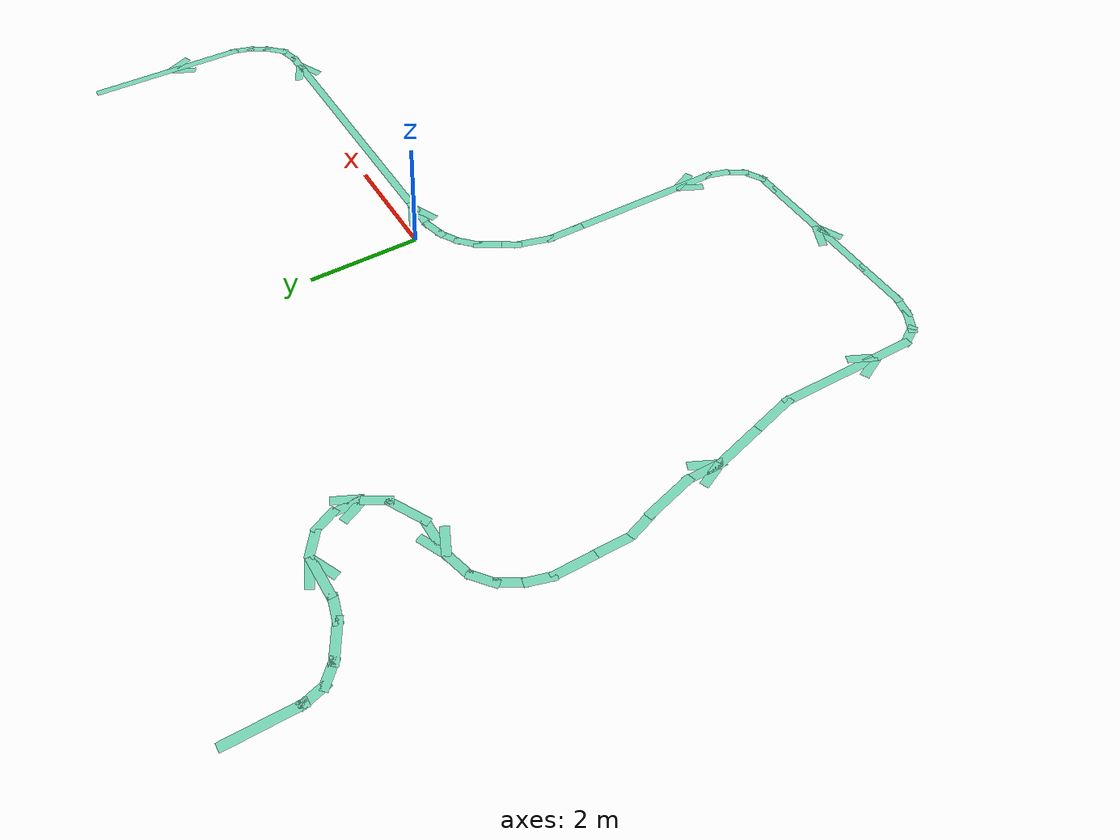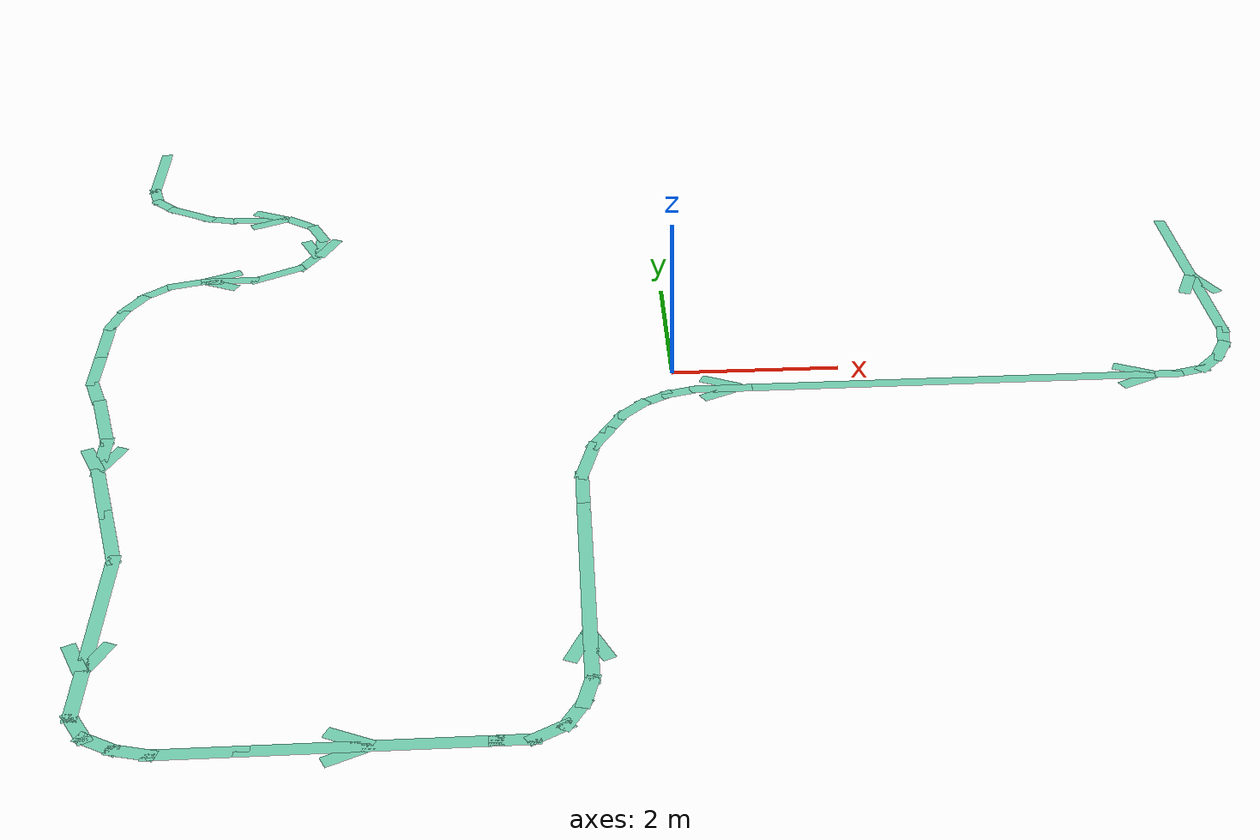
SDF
<?xml version='1.0'?>
<sdf version='1.6'>
  <model name='path_hospital'>
    <link name='Wall_10'>
      <pose frame=''>6.85995 0.436094 0 0 0 -1.8326</pose>
      <self_collide>0</self_collide>
      <enable_wind>0</enable_wind>
      <kinematic>0</kinematic>
      <visual name='Wall_10_Visual'>
        <pose frame=''>0 0 0 0 -0 0</pose>
        <geometry>
          <box>
            <size>0.5 0.15 0</size>
          </box>
        </geometry>
        <material>
          <script>
            <uri>file://media/materials/scripts/gazebo.material</uri>
            <name>Gazebo/Grey</name>
          </script>
          <ambient>0.435294 0.796078 0.67451 1</ambient>
          <shader type='pixel'/>
        </material>
        <meta>
          <layer>0</layer>
        </meta>
        <transparency>0</transparency>
        <cast_shadows>1</cast_shadows>
      </visual>
      <collision name='Wall_10_Collision'>
        <laser_retro>0</laser_retro>
        <max_contacts>10</max_contacts>
        <pose frame=''>0 0 0 0 -0 0</pose>
        <geometry>
          <box>
            <size>0.5 0.15 0</size>
          </box>
        </geometry>
        <surface>
          <friction>
            <ode>
              <mu>1</mu>
              <mu2>1</mu2>
              <fdir1>0 0 0</fdir1>
              <slip1>0</slip1>
              <slip2>0</slip2>
            </ode>
            <torsional>
              <coefficient>1</coefficient>
              <patch_radius>0</patch_radius>
              <surface_radius>0</surface_radius>
              <use_patch_radius>1</use_patch_radius>
              <ode>
                <slip>0</slip>
              </ode>
            </torsional>
          </friction>
          <bounce>
            <restitution_coefficient>0</restitution_coefficient>
            <threshold>1e+06</threshold>
          </bounce>
          <contact>
            <collide_without_contact>0</collide_without_contact>
            <collide_without_contact_bitmask>1</collide_without_contact_bitmask>
            <collide_bitmask>1</collide_bitmask>
            <ode>
              <soft_cfm>0</soft_cfm>
              <soft_erp>0.2</soft_erp>
              <kp>1e+13</kp>
              <kd>1</kd>
              <max_vel>0.01</max_vel>
              <min_depth>0</min_depth>
            </ode>
            <bullet>
              <split_impulse>1</split_impulse>
              <split_impulse_penetration_threshold>-0.01</split_impulse_penetration_threshold>
              <soft_cfm>0</soft_cfm>
              <soft_erp>0.2</soft_erp>
              <kp>1e+13</kp>
              <kd>1</kd>
            </bullet>
          </contact>
        </surface>
      </collision>
    </link>
    <link name='Wall_11'>
      <pose frame=''>6.72715 0.115501 0 0 0 -2.0944</pose>
      <self_collide>0</self_collide>
      <enable_wind>0</enable_wind>
      <kinematic>0</kinematic>
      <visual name='Wall_11_Visual'>
        <pose frame=''>0 0 0 0 -0 0</pose>
        <geometry>
          <box>
            <size>0.5 0.15 0</size>
          </box>
        </geometry>
        <material>
          <script>
            <uri>file://media/materials/scripts/gazebo.material</uri>
            <name>Gazebo/Grey</name>
          </script>
          <ambient>0.435294 0.796078 0.67451 1</ambient>
          <shader type='pixel'/>
        </material>
        <meta>
          <layer>0</layer>
        </meta>
        <transparency>0</transparency>
        <cast_shadows>1</cast_shadows>
      </visual>
      <collision name='Wall_11_Collision'>
        <laser_retro>0</laser_retro>
        <max_contacts>10</max_contacts>
        <pose frame=''>0 0 0 0 -0 0</pose>
        <geometry>
          <box>
            <size>0.5 0.15 0</size>
          </box>
        </geometry>
        <surface>
          <friction>
            <ode>
              <mu>1</mu>
              <mu2>1</mu2>
              <fdir1>0 0 0</fdir1>
              <slip1>0</slip1>
              <slip2>0</slip2>
            </ode>
            <torsional>
              <coefficient>1</coefficient>
              <patch_radius>0</patch_radius>
              <surface_radius>0</surface_radius>
              <use_patch_radius>1</use_patch_radius>
              <ode>
                <slip>0</slip>
              </ode>
            </torsional>
          </friction>
          <bounce>
            <restitution_coefficient>0</restitution_coefficient>
            <threshold>1e+06</threshold>
          </bounce>
          <contact>
            <collide_without_contact>0</collide_without_contact>
            <collide_without_contact_bitmask>1</collide_without_contact_bitmask>
            <collide_bitmask>1</collide_bitmask>
            <ode>
              <soft_cfm>0</soft_cfm>
              <soft_erp>0.2</soft_erp>
              <kp>1e+13</kp>
              <kd>1</kd>
              <max_vel>0.01</max_vel>
              <min_depth>0</min_depth>
            </ode>
            <bullet>
              <split_impulse>1</split_impulse>
              <split_impulse_penetration_threshold>-0.01</split_impulse_penetration_threshold>
              <soft_cfm>0</soft_cfm>
              <soft_erp>0.2</soft_erp>
              <kp>1e+13</kp>
              <kd>1</kd>
            </bullet>
          </contact>
        </surface>
      </collision>
    </link>
    <link name='Wall_12'>
      <pose frame=''>6.51591 -0.159796 0 0 0 -2.35619</pose>
      <self_collide>0</self_collide>
      <enable_wind>0</enable_wind>
      <kinematic>0</kinematic>
      <visual name='Wall_12_Visual'>
        <pose frame=''>0 0 0 0 -0 0</pose>
        <geometry>
          <box>
            <size>0.5 0.15 0</size>
          </box>
        </geometry>
        <material>
          <script>
            <uri>file://media/materials/scripts/gazebo.material</uri>
            <name>Gazebo/Grey</name>
          </script>
          <ambient>0.435294 0.796078 0.67451 1</ambient>
          <shader type='pixel'/>
        </material>
        <meta>
          <layer>0</layer>
        </meta>
        <transparency>0</transparency>
        <cast_shadows>1</cast_shadows>
      </visual>
      <collision name='Wall_12_Collision'>
        <laser_retro>0</laser_retro>
        <max_contacts>10</max_contacts>
        <pose frame=''>0 0 0 0 -0 0</pose>
        <geometry>
          <box>
            <size>0.5 0.15 0</size>
          </box>
        </geometry>
        <surface>
          <friction>
            <ode>
              <mu>1</mu>
              <mu2>1</mu2>
              <fdir1>0 0 0</fdir1>
              <slip1>0</slip1>
              <slip2>0</slip2>
            </ode>
            <torsional>
              <coefficient>1</coefficient>
              <patch_radius>0</patch_radius>
              <surface_radius>0</surface_radius>
              <use_patch_radius>1</use_patch_radius>
              <ode>
                <slip>0</slip>
              </ode>
            </torsional>
          </friction>
          <bounce>
            <restitution_coefficient>0</restitution_coefficient>
            <threshold>1e+06</threshold>
          </bounce>
          <contact>
            <collide_without_contact>0</collide_without_contact>
            <collide_without_contact_bitmask>1</collide_without_contact_bitmask>
            <collide_bitmask>1</collide_bitmask>
            <ode>
              <soft_cfm>0</soft_cfm>
              <soft_erp>0.2</soft_erp>
              <kp>1e+13</kp>
              <kd>1</kd>
              <max_vel>0.01</max_vel>
              <min_depth>0</min_depth>
            </ode>
            <bullet>
              <split_impulse>1</split_impulse>
              <split_impulse_penetration_threshold>-0.01</split_impulse_penetration_threshold>
              <soft_cfm>0</soft_cfm>
              <soft_erp>0.2</soft_erp>
              <kp>1e+13</kp>
              <kd>1</kd>
            </bullet>
          </contact>
        </surface>
      </collision>
    </link>
    <link name='Wall_13'>
      <pose frame=''>6.22313 -0.328833 0 0 0 -2.87979</pose>
      <self_collide>0</self_collide>
      <enable_wind>0</enable_wind>
      <kinematic>0</kinematic>
      <visual name='Wall_13_Visual'>
        <pose frame=''>0 0 0 0 -0 0</pose>
        <geometry>
          <box>
            <size>0.5 0.15 0</size>
          </box>
        </geometry>
        <material>
          <script>
            <uri>file://media/materials/scripts/gazebo.material</uri>
            <name>Gazebo/Grey</name>
          </script>
          <ambient>0.435294 0.796078 0.67451 1</ambient>
          <shader type='pixel'/>
        </material>
        <meta>
          <layer>0</layer>
        </meta>
        <transparency>0</transparency>
        <cast_shadows>1</cast_shadows>
      </visual>
      <collision name='Wall_13_Collision'>
        <laser_retro>0</laser_retro>
        <max_contacts>10</max_contacts>
        <pose frame=''>0 0 0 0 -0 0</pose>
        <geometry>
          <box>
            <size>0.5 0.15 0</size>
          </box>
        </geometry>
        <surface>
          <friction>
            <ode>
              <mu>1</mu>
              <mu2>1</mu2>
              <fdir1>0 0 0</fdir1>
              <slip1>0</slip1>
              <slip2>0</slip2>
            </ode>
            <torsional>
              <coefficient>1</coefficient>
              <patch_radius>0</patch_radius>
              <surface_radius>0</surface_radius>
              <use_patch_radius>1</use_patch_radius>
              <ode>
                <slip>0</slip>
              </ode>
            </torsional>
          </friction>
          <bounce>
            <restitution_coefficient>0</restitution_coefficient>
            <threshold>1e+06</threshold>
          </bounce>
          <contact>
            <collide_without_contact>0</collide_without_contact>
            <collide_without_contact_bitmask>1</collide_without_contact_bitmask>
            <collide_bitmask>1</collide_bitmask>
            <ode>
              <soft_cfm>0</soft_cfm>
              <soft_erp>0.2</soft_erp>
              <kp>1e+13</kp>
              <kd>1</kd>
              <max_vel>0.01</max_vel>
              <min_depth>0</min_depth>
            </ode>
            <bullet>
              <split_impulse>1</split_impulse>
              <split_impulse_penetration_threshold>-0.01</split_impulse_penetration_threshold>
              <soft_cfm>0</soft_cfm>
              <soft_erp>0.2</soft_erp>
              <kp>1e+13</kp>
              <kd>1</kd>
            </bullet>
          </contact>
        </surface>
      </collision>
    </link>
    <link name='Wall_14'>
      <pose frame=''>5.87909 -0.374126 0 0 -0 3.14159</pose>
      <self_collide>0</self_collide>
      <enable_wind>0</enable_wind>
      <kinematic>0</kinematic>
      <visual name='Wall_14_Visual'>
        <pose frame=''>0 0 0 0 -0 0</pose>
        <geometry>
          <box>
            <size>0.5 0.15 0</size>
          </box>
        </geometry>
        <material>
          <script>
            <uri>file://media/materials/scripts/gazebo.material</uri>
            <name>Gazebo/Grey</name>
          </script>
          <ambient>0.435294 0.796078 0.67451 1</ambient>
          <shader type='pixel'/>
        </material>
        <meta>
          <layer>0</layer>
        </meta>
        <transparency>0</transparency>
        <cast_shadows>1</cast_shadows>
      </visual>
      <collision name='Wall_14_Collision'>
        <laser_retro>0</laser_retro>
        <max_contacts>10</max_contacts>
        <pose frame=''>0 0 0 0 -0 0</pose>
        <geometry>
          <box>
            <size>0.5 0.15 0</size>
          </box>
        </geometry>
        <surface>
          <friction>
            <ode>
              <mu>1</mu>
              <mu2>1</mu2>
              <fdir1>0 0 0</fdir1>
              <slip1>0</slip1>
              <slip2>0</slip2>
            </ode>
            <torsional>
              <coefficient>1</coefficient>
              <patch_radius>0</patch_radius>
              <surface_radius>0</surface_radius>
              <use_patch_radius>1</use_patch_radius>
              <ode>
                <slip>0</slip>
              </ode>
            </torsional>
          </friction>
          <bounce>
            <restitution_coefficient>0</restitution_coefficient>
            <threshold>1e+06</threshold>
          </bounce>
          <contact>
            <collide_without_contact>0</collide_without_contact>
            <collide_without_contact_bitmask>1</collide_without_contact_bitmask>
            <collide_bitmask>1</collide_bitmask>
            <ode>
              <soft_cfm>0</soft_cfm>
              <soft_erp>0.2</soft_erp>
              <kp>1e+13</kp>
              <kd>1</kd>
              <max_vel>0.01</max_vel>
              <min_depth>0</min_depth>
            </ode>
            <bullet>
              <split_impulse>1</split_impulse>
              <split_impulse_penetration_threshold>-0.01</split_impulse_penetration_threshold>
              <soft_cfm>0</soft_cfm>
              <soft_erp>0.2</soft_erp>
              <kp>1e+13</kp>
              <kd>1</kd>
            </bullet>
          </contact>
        </surface>
      </collision>
    </link>
    <link name='Wall_15'>
      <pose frame=''>3.27909 -0.374126 0 0 -0 3.14159</pose>
      <self_collide>0</self_collide>
      <enable_wind>0</enable_wind>
      <kinematic>0</kinematic>
      <visual name='Wall_15_Visual'>
        <pose frame=''>0 0 0 0 -0 0</pose>
        <geometry>
          <box>
            <size>5 0.15 0</size>
          </box>
        </geometry>
        <material>
          <script>
            <uri>file://media/materials/scripts/gazebo.material</uri>
            <name>Gazebo/Grey</name>
          </script>
          <ambient>0.435294 0.796078 0.67451 1</ambient>
          <shader type='pixel'/>
        </material>
        <meta>
          <layer>0</layer>
        </meta>
        <transparency>0</transparency>
        <cast_shadows>1</cast_shadows>
      </visual>
      <collision name='Wall_15_Collision'>
        <laser_retro>0</laser_retro>
        <max_contacts>10</max_contacts>
        <pose frame=''>0 0 0 0 -0 0</pose>
        <geometry>
          <box>
            <size>5 0.15 0</size>
          </box>
        </geometry>
        <surface>
          <friction>
            <ode>
              <mu>1</mu>
              <mu2>1</mu2>
              <fdir1>0 0 0</fdir1>
              <slip1>0</slip1>
              <slip2>0</slip2>
            </ode>
            <torsional>
              <coefficient>1</coefficient>
              <patch_radius>0</patch_radius>
              <surface_radius>0</surface_radius>
              <use_patch_radius>1</use_patch_radius>
              <ode>
                <slip>0</slip>
              </ode>
            </torsional>
          </friction>
          <bounce>
            <restitution_coefficient>0</restitution_coefficient>
            <threshold>1e+06</threshold>
          </bounce>
          <contact>
            <collide_without_contact>0</collide_without_contact>
            <collide_without_contact_bitmask>1</collide_without_contact_bitmask>
            <collide_bitmask>1</collide_bitmask>
            <ode>
              <soft_cfm>0</soft_cfm>
              <soft_erp>0.2</soft_erp>
              <kp>1e+13</kp>
              <kd>1</kd>
              <max_vel>0.01</max_vel>
              <min_depth>0</min_depth>
            </ode>
            <bullet>
              <split_impulse>1</split_impulse>
              <split_impulse_penetration_threshold>-0.01</split_impulse_penetration_threshold>
              <soft_cfm>0</soft_cfm>
              <soft_erp>0.2</soft_erp>
              <kp>1e+13</kp>
              <kd>1</kd>
            </bullet>
          </contact>
        </surface>
      </collision>
    </link>
    <link name='Wall_16'>
      <pose frame=''>0.554091 -0.374126 0 0 -0 3.14159</pose>
      <self_collide>0</self_collide>
      <enable_wind>0</enable_wind>
      <kinematic>0</kinematic>
      <visual name='Wall_16_Visual'>
        <pose frame=''>0 0 0 0 -0 0</pose>
        <geometry>
          <box>
            <size>0.75 0.15 0</size>
          </box>
        </geometry>
        <material>
          <script>
            <uri>file://media/materials/scripts/gazebo.material</uri>
            <name>Gazebo/Grey</name>
          </script>
          <ambient>0.435294 0.796078 0.67451 1</ambient>
          <shader type='pixel'/>
        </material>
        <meta>
          <layer>0</layer>
        </meta>
        <transparency>0</transparency>
        <cast_shadows>1</cast_shadows>
      </visual>
      <collision name='Wall_16_Collision'>
        <laser_retro>0</laser_retro>
        <max_contacts>10</max_contacts>
        <pose frame=''>0 0 0 0 -0 0</pose>
        <geometry>
          <box>
            <size>0.75 0.15 0</size>
          </box>
        </geometry>
        <surface>
          <friction>
            <ode>
              <mu>1</mu>
              <mu2>1</mu2>
              <fdir1>0 0 0</fdir1>
              <slip1>0</slip1>
              <slip2>0</slip2>
            </ode>
            <torsional>
              <coefficient>1</coefficient>
              <patch_radius>0</patch_radius>
              <surface_radius>0</surface_radius>
              <use_patch_radius>1</use_patch_radius>
              <ode>
                <slip>0</slip>
              </ode>
            </torsional>
          </friction>
          <bounce>
            <restitution_coefficient>0</restitution_coefficient>
            <threshold>1e+06</threshold>
          </bounce>
          <contact>
            <collide_without_contact>0</collide_without_contact>
            <collide_without_contact_bitmask>1</collide_without_contact_bitmask>
            <collide_bitmask>1</collide_bitmask>
            <ode>
              <soft_cfm>0</soft_cfm>
              <soft_erp>0.2</soft_erp>
              <kp>1e+13</kp>
              <kd>1</kd>
              <max_vel>0.01</max_vel>
              <min_depth>0</min_depth>
            </ode>
            <bullet>
              <split_impulse>1</split_impulse>
              <split_impulse_penetration_threshold>-0.01</split_impulse_penetration_threshold>
              <soft_cfm>0</soft_cfm>
              <soft_erp>0.2</soft_erp>
              <kp>1e+13</kp>
              <kd>1</kd>
            </bullet>
          </contact>
        </surface>
      </collision>
    </link>
    <link name='Wall_17'>
      <pose frame=''>0.085054 -0.41942 0 0 0 -2.87979</pose>
      <self_collide>0</self_collide>
      <enable_wind>0</enable_wind>
      <kinematic>0</kinematic>
      <visual name='Wall_17_Visual'>
        <pose frame=''>0 0 0 0 -0 0</pose>
        <geometry>
          <box>
            <size>0.5 0.15 0</size>
          </box>
        </geometry>
        <material>
          <script>
            <uri>file://media/materials/scripts/gazebo.material</uri>
            <name>Gazebo/Grey</name>
          </script>
          <ambient>0.435294 0.796078 0.67451 1</ambient>
          <shader type='pixel'/>
        </material>
        <meta>
          <layer>0</layer>
        </meta>
        <transparency>0</transparency>
        <cast_shadows>1</cast_shadows>
      </visual>
      <collision name='Wall_17_Collision'>
        <laser_retro>0</laser_retro>
        <max_contacts>10</max_contacts>
        <pose frame=''>0 0 0 0 -0 0</pose>
        <geometry>
          <box>
            <size>0.5 0.15 0</size>
          </box>
        </geometry>
        <surface>
          <friction>
            <ode>
              <mu>1</mu>
              <mu2>1</mu2>
              <fdir1>0 0 0</fdir1>
              <slip1>0</slip1>
              <slip2>0</slip2>
            </ode>
            <torsional>
              <coefficient>1</coefficient>
              <patch_radius>0</patch_radius>
              <surface_radius>0</surface_radius>
              <use_patch_radius>1</use_patch_radius>
              <ode>
                <slip>0</slip>
              </ode>
            </torsional>
          </friction>
          <bounce>
            <restitution_coefficient>0</restitution_coefficient>
            <threshold>1e+06</threshold>
          </bounce>
          <contact>
            <collide_without_contact>0</collide_without_contact>
            <collide_without_contact_bitmask>1</collide_without_contact_bitmask>
            <collide_bitmask>1</collide_bitmask>
            <ode>
              <soft_cfm>0</soft_cfm>
              <soft_erp>0.2</soft_erp>
              <kp>1e+13</kp>
              <kd>1</kd>
              <max_vel>0.01</max_vel>
              <min_depth>0</min_depth>
            </ode>
            <bullet>
              <split_impulse>1</split_impulse>
              <split_impulse_penetration_threshold>-0.01</split_impulse_penetration_threshold>
              <soft_cfm>0</soft_cfm>
              <soft_erp>0.2</soft_erp>
              <kp>1e+13</kp>
              <kd>1</kd>
            </bullet>
          </contact>
        </surface>
      </collision>
    </link>
    <link name='Wall_18'>
      <pose frame=''>-0.235537 -0.552214 0 0 0 -2.61799</pose>
      <self_collide>0</self_collide>
      <enable_wind>0</enable_wind>
      <kinematic>0</kinematic>
      <visual name='Wall_18_Visual'>
        <pose frame=''>0 0 0 0 -0 0</pose>
        <geometry>
          <box>
            <size>0.5 0.15 0</size>
          </box>
        </geometry>
        <material>
          <script>
            <uri>file://media/materials/scripts/gazebo.material</uri>
            <name>Gazebo/Grey</name>
          </script>
          <ambient>0.435294 0.796078 0.67451 1</ambient>
          <shader type='pixel'/>
        </material>
        <meta>
          <layer>0</layer>
        </meta>
        <transparency>0</transparency>
        <cast_shadows>1</cast_shadows>
      </visual>
      <collision name='Wall_18_Collision'>
        <laser_retro>0</laser_retro>
        <max_contacts>10</max_contacts>
        <pose frame=''>0 0 0 0 -0 0</pose>
        <geometry>
          <box>
            <size>0.5 0.15 0</size>
          </box>
        </geometry>
        <surface>
          <friction>
            <ode>
              <mu>1</mu>
              <mu2>1</mu2>
              <fdir1>0 0 0</fdir1>
              <slip1>0</slip1>
              <slip2>0</slip2>
            </ode>
            <torsional>
              <coefficient>1</coefficient>
              <patch_radius>0</patch_radius>
              <surface_radius>0</surface_radius>
              <use_patch_radius>1</use_patch_radius>
              <ode>
                <slip>0</slip>
              </ode>
            </torsional>
          </friction>
          <bounce>
            <restitution_coefficient>0</restitution_coefficient>
            <threshold>1e+06</threshold>
          </bounce>
          <contact>
            <collide_without_contact>0</collide_without_contact>
            <collide_without_contact_bitmask>1</collide_without_contact_bitmask>
            <collide_bitmask>1</collide_bitmask>
            <ode>
              <soft_cfm>0</soft_cfm>
              <soft_erp>0.2</soft_erp>
              <kp>1e+13</kp>
              <kd>1</kd>
              <max_vel>0.01</max_vel>
              <min_depth>0</min_depth>
            </ode>
            <bullet>
              <split_impulse>1</split_impulse>
              <split_impulse_penetration_threshold>-0.01</split_impulse_penetration_threshold>
              <soft_cfm>0</soft_cfm>
              <soft_erp>0.2</soft_erp>
              <kp>1e+13</kp>
              <kd>1</kd>
            </bullet>
          </contact>
        </surface>
      </collision>
    </link>
    <link name='Wall_19'>
      <pose frame=''>-0.510835 -0.763456 0 0 0 -2.35619</pose>
      <self_collide>0</self_collide>
      <enable_wind>0</enable_wind>
      <kinematic>0</kinematic>
      <visual name='Wall_19_Visual'>
        <pose frame=''>0 0 0 0 -0 0</pose>
        <geometry>
          <box>
            <size>0.5 0.15 0</size>
          </box>
        </geometry>
        <material>
          <script>
            <uri>file://media/materials/scripts/gazebo.material</uri>
            <name>Gazebo/Grey</name>
          </script>
          <ambient>0.435294 0.796078 0.67451 1</ambient>
          <shader type='pixel'/>
        </material>
        <meta>
          <layer>0</layer>
        </meta>
        <transparency>0</transparency>
        <cast_shadows>1</cast_shadows>
      </visual>
      <collision name='Wall_19_Collision'>
        <laser_retro>0</laser_retro>
        <max_contacts>10</max_contacts>
        <pose frame=''>0 0 0 0 -0 0</pose>
        <geometry>
          <box>
            <size>0.5 0.15 0</size>
          </box>
        </geometry>
        <surface>
          <friction>
            <ode>
              <mu>1</mu>
              <mu2>1</mu2>
              <fdir1>0 0 0</fdir1>
              <slip1>0</slip1>
              <slip2>0</slip2>
            </ode>
            <torsional>
              <coefficient>1</coefficient>
              <patch_radius>0</patch_radius>
              <surface_radius>0</surface_radius>
              <use_patch_radius>1</use_patch_radius>
              <ode>
                <slip>0</slip>
              </ode>
            </torsional>
          </friction>
          <bounce>
            <restitution_coefficient>0</restitution_coefficient>
            <threshold>1e+06</threshold>
          </bounce>
          <contact>
            <collide_without_contact>0</collide_without_contact>
            <collide_without_contact_bitmask>1</collide_without_contact_bitmask>
            <collide_bitmask>1</collide_bitmask>
            <ode>
              <soft_cfm>0</soft_cfm>
              <soft_erp>0.2</soft_erp>
              <kp>1e+13</kp>
              <kd>1</kd>
              <max_vel>0.01</max_vel>
              <min_depth>0</min_depth>
            </ode>
            <bullet>
              <split_impulse>1</split_impulse>
              <split_impulse_penetration_threshold>-0.01</split_impulse_penetration_threshold>
              <soft_cfm>0</soft_cfm>
              <soft_erp>0.2</soft_erp>
              <kp>1e+13</kp>
              <kd>1</kd>
            </bullet>
          </contact>
        </surface>
      </collision>
    </link>
    <link name='Wall_20'>
      <pose frame=''>-0.722079 -1.03876 0 0 0 -2.0944</pose>
      <self_collide>0</self_collide>
      <enable_wind>0</enable_wind>
      <kinematic>0</kinematic>
      <visual name='Wall_20_Visual'>
        <pose frame=''>0 0 0 0 -0 0</pose>
        <geometry>
          <box>
            <size>0.5 0.15 0</size>
          </box>
        </geometry>
        <material>
          <script>
            <uri>file://media/materials/scripts/gazebo.material</uri>
            <name>Gazebo/Grey</name>
          </script>
          <ambient>0.435294 0.796078 0.67451 1</ambient>
          <shader type='pixel'/>
        </material>
        <meta>
          <layer>0</layer>
        </meta>
        <transparency>0</transparency>
        <cast_shadows>1</cast_shadows>
      </visual>
      <collision name='Wall_20_Collision'>
        <laser_retro>0</laser_retro>
        <max_contacts>10</max_contacts>
        <pose frame=''>0 0 0 0 -0 0</pose>
        <geometry>
          <box>
            <size>0.5 0.15 0</size>
          </box>
        </geometry>
        <surface>
          <friction>
            <ode>
              <mu>1</mu>
              <mu2>1</mu2>
              <fdir1>0 0 0</fdir1>
              <slip1>0</slip1>
              <slip2>0</slip2>
            </ode>
            <torsional>
              <coefficient>1</coefficient>
              <patch_radius>0</patch_radius>
              <surface_radius>0</surface_radius>
              <use_patch_radius>1</use_patch_radius>
              <ode>
                <slip>0</slip>
              </ode>
            </torsional>
          </friction>
          <bounce>
            <restitution_coefficient>0</restitution_coefficient>
            <threshold>1e+06</threshold>
          </bounce>
          <contact>
            <collide_without_contact>0</collide_without_contact>
            <collide_without_contact_bitmask>1</collide_without_contact_bitmask>
            <collide_bitmask>1</collide_bitmask>
            <ode>
              <soft_cfm>0</soft_cfm>
              <soft_erp>0.2</soft_erp>
              <kp>1e+13</kp>
              <kd>1</kd>
              <max_vel>0.01</max_vel>
              <min_depth>0</min_depth>
            </ode>
            <bullet>
              <split_impulse>1</split_impulse>
              <split_impulse_penetration_threshold>-0.01</split_impulse_penetration_threshold>
              <soft_cfm>0</soft_cfm>
              <soft_erp>0.2</soft_erp>
              <kp>1e+13</kp>
              <kd>1</kd>
            </bullet>
          </contact>
        </surface>
      </collision>
    </link>
    <link name='Wall_21'>
      <pose frame=''>-0.897079 -1.34186 0 0 0 -2.0944</pose>
      <self_collide>0</self_collide>
      <enable_wind>0</enable_wind>
      <kinematic>0</kinematic>
      <visual name='Wall_21_Visual'>
        <pose frame=''>0 0 0 0 -0 0</pose>
        <geometry>
          <box>
            <size>0.5 0.15 0</size>
          </box>
        </geometry>
        <material>
          <script>
            <uri>file://media/materials/scripts/gazebo.material</uri>
            <name>Gazebo/Grey</name>
          </script>
          <ambient>0.435294 0.796078 0.67451 1</ambient>
          <shader type='pixel'/>
        </material>
        <meta>
          <layer>0</layer>
        </meta>
        <transparency>0</transparency>
        <cast_shadows>1</cast_shadows>
      </visual>
      <collision name='Wall_21_Collision'>
        <laser_retro>0</laser_retro>
        <max_contacts>10</max_contacts>
        <pose frame=''>0 0 0 0 -0 0</pose>
        <geometry>
          <box>
            <size>0.5 0.15 0</size>
          </box>
        </geometry>
        <surface>
          <friction>
            <ode>
              <mu>1</mu>
              <mu2>1</mu2>
              <fdir1>0 0 0</fdir1>
              <slip1>0</slip1>
              <slip2>0</slip2>
            </ode>
            <torsional>
              <coefficient>1</coefficient>
              <patch_radius>0</patch_radius>
              <surface_radius>0</surface_radius>
              <use_patch_radius>1</use_patch_radius>
              <ode>
                <slip>0</slip>
              </ode>
            </torsional>
          </friction>
          <bounce>
            <restitution_coefficient>0</restitution_coefficient>
            <threshold>1e+06</threshold>
          </bounce>
          <contact>
            <collide_without_contact>0</collide_without_contact>
            <collide_without_contact_bitmask>1</collide_without_contact_bitmask>
            <collide_bitmask>1</collide_bitmask>
            <ode>
              <soft_cfm>0</soft_cfm>
              <soft_erp>0.2</soft_erp>
              <kp>1e+13</kp>
              <kd>1</kd>
              <max_vel>0.01</max_vel>
              <min_depth>0</min_depth>
            </ode>
            <bullet>
              <split_impulse>1</split_impulse>
              <split_impulse_penetration_threshold>-0.01</split_impulse_penetration_threshold>
              <soft_cfm>0</soft_cfm>
              <soft_erp>0.2</soft_erp>
              <kp>1e+13</kp>
              <kd>1</kd>
            </bullet>
          </contact>
        </surface>
      </collision>
    </link>
    <link name='Wall_22'>
      <pose frame=''>-1.06222 -1.7832 0 0 0 -1.8326</pose>
      <self_collide>0</self_collide>
      <enable_wind>0</enable_wind>
      <kinematic>0</kinematic>
      <visual name='Wall_22_Visual'>
        <pose frame=''>0 0 0 0 -0 0</pose>
        <geometry>
          <box>
            <size>0.75 0.15 0</size>
          </box>
        </geometry>
        <material>
          <script>
            <uri>file://media/materials/scripts/gazebo.material</uri>
            <name>Gazebo/Grey</name>
          </script>
          <ambient>0.435294 0.796078 0.67451 1</ambient>
          <shader type='pixel'/>
        </material>
        <meta>
          <layer>0</layer>
        </meta>
        <transparency>0</transparency>
        <cast_shadows>1</cast_shadows>
      </visual>
      <collision name='Wall_22_Collision'>
        <laser_retro>0</laser_retro>
        <max_contacts>10</max_contacts>
        <pose frame=''>0 0 0 0 -0 0</pose>
        <geometry>
          <box>
            <size>0.75 0.15 0</size>
          </box>
        </geometry>
        <surface>
          <friction>
            <ode>
              <mu>1</mu>
              <mu2>1</mu2>
              <fdir1>0 0 0</fdir1>
              <slip1>0</slip1>
              <slip2>0</slip2>
            </ode>
            <torsional>
              <coefficient>1</coefficient>
              <patch_radius>0</patch_radius>
              <surface_radius>0</surface_radius>
              <use_patch_radius>1</use_patch_radius>
              <ode>
                <slip>0</slip>
              </ode>
            </torsional>
          </friction>
          <bounce>
            <restitution_coefficient>0</restitution_coefficient>
            <threshold>1e+06</threshold>
          </bounce>
          <contact>
            <collide_without_contact>0</collide_without_contact>
            <collide_without_contact_bitmask>1</collide_without_contact_bitmask>
            <collide_bitmask>1</collide_bitmask>
            <ode>
              <soft_cfm>0</soft_cfm>
              <soft_erp>0.2</soft_erp>
              <kp>1e+13</kp>
              <kd>1</kd>
              <max_vel>0.01</max_vel>
              <min_depth>0</min_depth>
            </ode>
            <bullet>
              <split_impulse>1</split_impulse>
              <split_impulse_penetration_threshold>-0.01</split_impulse_penetration_threshold>
              <soft_cfm>0</soft_cfm>
              <soft_erp>0.2</soft_erp>
              <kp>1e+13</kp>
              <kd>1</kd>
            </bullet>
          </contact>
        </surface>
      </collision>
    </link>
    <link name='Wall_23'>
      <pose frame=''>-1.13987 -2.37297 0 0 0 -1.5708</pose>
      <self_collide>0</self_collide>
      <enable_wind>0</enable_wind>
      <kinematic>0</kinematic>
      <visual name='Wall_23_Visual'>
        <pose frame=''>0 0 0 0 -0 0</pose>
        <geometry>
          <box>
            <size>0.75 0.15 0</size>
          </box>
        </geometry>
        <material>
          <script>
            <uri>file://media/materials/scripts/gazebo.material</uri>
            <name>Gazebo/Grey</name>
          </script>
          <ambient>0.435294 0.796078 0.67451 1</ambient>
          <shader type='pixel'/>
        </material>
        <meta>
          <layer>0</layer>
        </meta>
        <transparency>0</transparency>
        <cast_shadows>1</cast_shadows>
      </visual>
      <collision name='Wall_23_Collision'>
        <laser_retro>0</laser_retro>
        <max_contacts>10</max_contacts>
        <pose frame=''>0 0 0 0 -0 0</pose>
        <geometry>
          <box>
            <size>0.75 0.15 0</size>
          </box>
        </geometry>
        <surface>
          <friction>
            <ode>
              <mu>1</mu>
              <mu2>1</mu2>
              <fdir1>0 0 0</fdir1>
              <slip1>0</slip1>
              <slip2>0</slip2>
            </ode>
            <torsional>
              <coefficient>1</coefficient>
              <patch_radius>0</patch_radius>
              <surface_radius>0</surface_radius>
              <use_patch_radius>1</use_patch_radius>
              <ode>
                <slip>0</slip>
              </ode>
            </torsional>
          </friction>
          <bounce>
            <restitution_coefficient>0</restitution_coefficient>
            <threshold>1e+06</threshold>
          </bounce>
          <contact>
            <collide_without_contact>0</collide_without_contact>
            <collide_without_contact_bitmask>1</collide_without_contact_bitmask>
            <collide_bitmask>1</collide_bitmask>
            <ode>
              <soft_cfm>0</soft_cfm>
              <soft_erp>0.2</soft_erp>
              <kp>1e+13</kp>
              <kd>1</kd>
              <max_vel>0.01</max_vel>
              <min_depth>0</min_depth>
            </ode>
            <bullet>
              <split_impulse>1</split_impulse>
              <split_impulse_penetration_threshold>-0.01</split_impulse_penetration_threshold>
              <soft_cfm>0</soft_cfm>
              <soft_erp>0.2</soft_erp>
              <kp>1e+13</kp>
              <kd>1</kd>
            </bullet>
          </contact>
        </surface>
      </collision>
    </link>
    <link name='Wall_24'>
      <pose frame=''>-1.13987 -4.09797 0 0 0 -1.5708</pose>
      <self_collide>0</self_collide>
      <enable_wind>0</enable_wind>
      <kinematic>0</kinematic>
      <visual name='Wall_24_Visual'>
        <pose frame=''>0 0 0 0 -0 0</pose>
        <geometry>
          <box>
            <size>3 0.15 0</size>
          </box>
        </geometry>
        <material>
          <script>
            <uri>file://media/materials/scripts/gazebo.material</uri>
            <name>Gazebo/Grey</name>
          </script>
          <ambient>0.435294 0.796078 0.67451 1</ambient>
          <shader type='pixel'/>
        </material>
        <meta>
          <layer>0</layer>
        </meta>
        <transparency>0</transparency>
        <cast_shadows>1</cast_shadows>
      </visual>
      <collision name='Wall_24_Collision'>
        <laser_retro>0</laser_retro>
        <max_contacts>10</max_contacts>
        <pose frame=''>0 0 0 0 -0 0</pose>
        <geometry>
          <box>
            <size>3 0.15 0</size>
          </box>
        </geometry>
        <surface>
          <friction>
            <ode>
              <mu>1</mu>
              <mu2>1</mu2>
              <fdir1>0 0 0</fdir1>
              <slip1>0</slip1>
              <slip2>0</slip2>
            </ode>
            <torsional>
              <coefficient>1</coefficient>
              <patch_radius>0</patch_radius>
              <surface_radius>0</surface_radius>
              <use_patch_radius>1</use_patch_radius>
              <ode>
                <slip>0</slip>
              </ode>
            </torsional>
          </friction>
          <bounce>
            <restitution_coefficient>0</restitution_coefficient>
            <threshold>1e+06</threshold>
          </bounce>
          <contact>
            <collide_without_contact>0</collide_without_contact>
            <collide_without_contact_bitmask>1</collide_without_contact_bitmask>
            <collide_bitmask>1</collide_bitmask>
            <ode>
              <soft_cfm>0</soft_cfm>
              <soft_erp>0.2</soft_erp>
              <kp>1e+13</kp>
              <kd>1</kd>
              <max_vel>0.01</max_vel>
              <min_depth>0</min_depth>
            </ode>
            <bullet>
              <split_impulse>1</split_impulse>
              <split_impulse_penetration_threshold>-0.01</split_impulse_penetration_threshold>
              <soft_cfm>0</soft_cfm>
              <soft_erp>0.2</soft_erp>
              <kp>1e+13</kp>
              <kd>1</kd>
            </bullet>
          </contact>
        </surface>
      </collision>
    </link>
    <link name='Wall_25'>
      <pose frame=''>-1.18516 -5.69201 0 0 0 -1.8326</pose>
      <self_collide>0</self_collide>
      <enable_wind>0</enable_wind>
      <kinematic>0</kinematic>
      <visual name='Wall_25_Visual'>
        <pose frame=''>0 0 0 0 -0 0</pose>
        <geometry>
          <box>
            <size>0.5 0.15 0</size>
          </box>
        </geometry>
        <material>
          <script>
            <uri>file://media/materials/scripts/gazebo.material</uri>
            <name>Gazebo/Grey</name>
          </script>
          <ambient>0.435294 0.796078 0.67451 1</ambient>
          <shader type='pixel'/>
        </material>
        <meta>
          <layer>0</layer>
        </meta>
        <transparency>0</transparency>
        <cast_shadows>1</cast_shadows>
      </visual>
      <collision name='Wall_25_Collision'>
        <laser_retro>0</laser_retro>
        <max_contacts>10</max_contacts>
        <pose frame=''>0 0 0 0 -0 0</pose>
        <geometry>
          <box>
            <size>0.5 0.15 0</size>
          </box>
        </geometry>
        <surface>
          <friction>
            <ode>
              <mu>1</mu>
              <mu2>1</mu2>
              <fdir1>0 0 0</fdir1>
              <slip1>0</slip1>
              <slip2>0</slip2>
            </ode>
            <torsional>
              <coefficient>1</coefficient>
              <patch_radius>0</patch_radius>
              <surface_radius>0</surface_radius>
              <use_patch_radius>1</use_patch_radius>
              <ode>
                <slip>0</slip>
              </ode>
            </torsional>
          </friction>
          <bounce>
            <restitution_coefficient>0</restitution_coefficient>
            <threshold>1e+06</threshold>
          </bounce>
          <contact>
            <collide_without_contact>0</collide_without_contact>
            <collide_without_contact_bitmask>1</collide_without_contact_bitmask>
            <collide_bitmask>1</collide_bitmask>
            <ode>
              <soft_cfm>0</soft_cfm>
              <soft_erp>0.2</soft_erp>
              <kp>1e+13</kp>
              <kd>1</kd>
              <max_vel>0.01</max_vel>
              <min_depth>0</min_depth>
            </ode>
            <bullet>
              <split_impulse>1</split_impulse>
              <split_impulse_penetration_threshold>-0.01</split_impulse_penetration_threshold>
              <soft_cfm>0</soft_cfm>
              <soft_erp>0.2</soft_erp>
              <kp>1e+13</kp>
              <kd>1</kd>
            </bullet>
          </contact>
        </surface>
      </collision>
    </link>
    <link name='Wall_26'>
      <pose frame=''>-1.31796 -6.0126 0 0 0 -2.0944</pose>
      <self_collide>0</self_collide>
      <enable_wind>0</enable_wind>
      <kinematic>0</kinematic>
      <visual name='Wall_26_Visual'>
        <pose frame=''>0 0 0 0 -0 0</pose>
        <geometry>
          <box>
            <size>0.5 0.15 0</size>
          </box>
        </geometry>
        <material>
          <script>
            <uri>file://media/materials/scripts/gazebo.material</uri>
            <name>Gazebo/Grey</name>
          </script>
          <ambient>0.435294 0.796078 0.67451 1</ambient>
          <shader type='pixel'/>
        </material>
        <meta>
          <layer>0</layer>
        </meta>
        <transparency>0</transparency>
        <cast_shadows>1</cast_shadows>
      </visual>
      <collision name='Wall_26_Collision'>
        <laser_retro>0</laser_retro>
        <max_contacts>10</max_contacts>
        <pose frame=''>0 0 0 0 -0 0</pose>
        <geometry>
          <box>
            <size>0.5 0.15 0</size>
          </box>
        </geometry>
        <surface>
          <friction>
            <ode>
              <mu>1</mu>
              <mu2>1</mu2>
              <fdir1>0 0 0</fdir1>
              <slip1>0</slip1>
              <slip2>0</slip2>
            </ode>
            <torsional>
              <coefficient>1</coefficient>
              <patch_radius>0</patch_radius>
              <surface_radius>0</surface_radius>
              <use_patch_radius>1</use_patch_radius>
              <ode>
                <slip>0</slip>
              </ode>
            </torsional>
          </friction>
          <bounce>
            <restitution_coefficient>0</restitution_coefficient>
            <threshold>1e+06</threshold>
          </bounce>
          <contact>
            <collide_without_contact>0</collide_without_contact>
            <collide_without_contact_bitmask>1</collide_without_contact_bitmask>
            <collide_bitmask>1</collide_bitmask>
            <ode>
              <soft_cfm>0</soft_cfm>
              <soft_erp>0.2</soft_erp>
              <kp>1e+13</kp>
              <kd>1</kd>
              <max_vel>0.01</max_vel>
              <min_depth>0</min_depth>
            </ode>
            <bullet>
              <split_impulse>1</split_impulse>
              <split_impulse_penetration_threshold>-0.01</split_impulse_penetration_threshold>
              <soft_cfm>0</soft_cfm>
              <soft_erp>0.2</soft_erp>
              <kp>1e+13</kp>
              <kd>1</kd>
            </bullet>
          </contact>
        </surface>
      </collision>
    </link>
    <link name='Wall_27'>
      <pose frame=''>-1.55701 -6.25166 0 0 0 -2.61799</pose>
      <self_collide>0</self_collide>
      <enable_wind>0</enable_wind>
      <kinematic>0</kinematic>
      <visual name='Wall_27_Visual'>
        <pose frame=''>0 0 0 0 -0 0</pose>
        <geometry>
          <box>
            <size>0.5 0.15 0</size>
          </box>
        </geometry>
        <material>
          <script>
            <uri>file://media/materials/scripts/gazebo.material</uri>
            <name>Gazebo/Grey</name>
          </script>
          <ambient>0.435294 0.796078 0.67451 1</ambient>
          <shader type='pixel'/>
        </material>
        <meta>
          <layer>0</layer>
        </meta>
        <transparency>0</transparency>
        <cast_shadows>1</cast_shadows>
      </visual>
      <collision name='Wall_27_Collision'>
        <laser_retro>0</laser_retro>
        <max_contacts>10</max_contacts>
        <pose frame=''>0 0 0 0 -0 0</pose>
        <geometry>
          <box>
            <size>0.5 0.15 0</size>
          </box>
        </geometry>
        <surface>
          <friction>
            <ode>
              <mu>1</mu>
              <mu2>1</mu2>
              <fdir1>0 0 0</fdir1>
              <slip1>0</slip1>
              <slip2>0</slip2>
            </ode>
            <torsional>
              <coefficient>1</coefficient>
              <patch_radius>0</patch_radius>
              <surface_radius>0</surface_radius>
              <use_patch_radius>1</use_patch_radius>
              <ode>
                <slip>0</slip>
              </ode>
            </torsional>
          </friction>
          <bounce>
            <restitution_coefficient>0</restitution_coefficient>
            <threshold>1e+06</threshold>
          </bounce>
          <contact>
            <collide_without_contact>0</collide_without_contact>
            <collide_without_contact_bitmask>1</collide_without_contact_bitmask>
            <collide_bitmask>1</collide_bitmask>
            <ode>
              <soft_cfm>0</soft_cfm>
              <soft_erp>0.2</soft_erp>
              <kp>1e+13</kp>
              <kd>1</kd>
              <max_vel>0.01</max_vel>
              <min_depth>0</min_depth>
            </ode>
            <bullet>
              <split_impulse>1</split_impulse>
              <split_impulse_penetration_threshold>-0.01</split_impulse_penetration_threshold>
              <soft_cfm>0</soft_cfm>
              <soft_erp>0.2</soft_erp>
              <kp>1e+13</kp>
              <kd>1</kd>
            </bullet>
          </contact>
        </surface>
      </collision>
    </link>
    <link name='Wall_28'>
      <pose frame=''>-1.88357 -6.33915 0 0 -0 3.14159</pose>
      <self_collide>0</self_collide>
      <enable_wind>0</enable_wind>
      <kinematic>0</kinematic>
      <visual name='Wall_28_Visual'>
        <pose frame=''>0 0 0 0 -0 0</pose>
        <geometry>
          <box>
            <size>0.5 0.15 0</size>
          </box>
        </geometry>
        <material>
          <script>
            <uri>file://media/materials/scripts/gazebo.material</uri>
            <name>Gazebo/Grey</name>
          </script>
          <ambient>0.435294 0.796078 0.67451 1</ambient>
          <shader type='pixel'/>
        </material>
        <meta>
          <layer>0</layer>
        </meta>
        <transparency>0</transparency>
        <cast_shadows>1</cast_shadows>
      </visual>
      <collision name='Wall_28_Collision'>
        <laser_retro>0</laser_retro>
        <max_contacts>10</max_contacts>
        <pose frame=''>0 0 0 0 -0 0</pose>
        <geometry>
          <box>
            <size>0.5 0.15 0</size>
          </box>
        </geometry>
        <surface>
          <friction>
            <ode>
              <mu>1</mu>
              <mu2>1</mu2>
              <fdir1>0 0 0</fdir1>
              <slip1>0</slip1>
              <slip2>0</slip2>
            </ode>
            <torsional>
              <coefficient>1</coefficient>
              <patch_radius>0</patch_radius>
              <surface_radius>0</surface_radius>
              <use_patch_radius>1</use_patch_radius>
              <ode>
                <slip>0</slip>
              </ode>
            </torsional>
          </friction>
          <bounce>
            <restitution_coefficient>0</restitution_coefficient>
            <threshold>1e+06</threshold>
          </bounce>
          <contact>
            <collide_without_contact>0</collide_without_contact>
            <collide_without_contact_bitmask>1</collide_without_contact_bitmask>
            <collide_bitmask>1</collide_bitmask>
            <ode>
              <soft_cfm>0</soft_cfm>
              <soft_erp>0.2</soft_erp>
              <kp>1e+13</kp>
              <kd>1</kd>
              <max_vel>0.01</max_vel>
              <min_depth>0</min_depth>
            </ode>
            <bullet>
              <split_impulse>1</split_impulse>
              <split_impulse_penetration_threshold>-0.01</split_impulse_penetration_threshold>
              <soft_cfm>0</soft_cfm>
              <soft_erp>0.2</soft_erp>
              <kp>1e+13</kp>
              <kd>1</kd>
            </bullet>
          </contact>
        </surface>
      </collision>
    </link>
    <link name='Wall_29'>
      <pose frame=''>-3.23357 -6.33915 0 0 -0 3.14159</pose>
      <self_collide>0</self_collide>
      <enable_wind>0</enable_wind>
      <kinematic>0</kinematic>
      <visual name='Wall_29_Visual'>
        <pose frame=''>0 0 0 0 -0 0</pose>
        <geometry>
          <box>
            <size>2.5 0.15 0</size>
          </box>
        </geometry>
        <material>
          <script>
            <uri>file://media/materials/scripts/gazebo.material</uri>
            <name>Gazebo/Grey</name>
          </script>
          <ambient>0.435294 0.796078 0.67451 1</ambient>
          <shader type='pixel'/>
        </material>
        <meta>
          <layer>0</layer>
        </meta>
        <transparency>0</transparency>
        <cast_shadows>1</cast_shadows>
      </visual>
      <collision name='Wall_29_Collision'>
        <laser_retro>0</laser_retro>
        <max_contacts>10</max_contacts>
        <pose frame=''>0 0 0 0 -0 0</pose>
        <geometry>
          <box>
            <size>2.5 0.15 0</size>
          </box>
        </geometry>
        <surface>
          <friction>
            <ode>
              <mu>1</mu>
              <mu2>1</mu2>
              <fdir1>0 0 0</fdir1>
              <slip1>0</slip1>
              <slip2>0</slip2>
            </ode>
            <torsional>
              <coefficient>1</coefficient>
              <patch_radius>0</patch_radius>
              <surface_radius>0</surface_radius>
              <use_patch_radius>1</use_patch_radius>
              <ode>
                <slip>0</slip>
              </ode>
            </torsional>
          </friction>
          <bounce>
            <restitution_coefficient>0</restitution_coefficient>
            <threshold>1e+06</threshold>
          </bounce>
          <contact>
            <collide_without_contact>0</collide_without_contact>
            <collide_without_contact_bitmask>1</collide_without_contact_bitmask>
            <collide_bitmask>1</collide_bitmask>
            <ode>
              <soft_cfm>0</soft_cfm>
              <soft_erp>0.2</soft_erp>
              <kp>1e+13</kp>
              <kd>1</kd>
              <max_vel>0.01</max_vel>
              <min_depth>0</min_depth>
            </ode>
            <bullet>
              <split_impulse>1</split_impulse>
              <split_impulse_penetration_threshold>-0.01</split_impulse_penetration_threshold>
              <soft_cfm>0</soft_cfm>
              <soft_erp>0.2</soft_erp>
              <kp>1e+13</kp>
              <kd>1</kd>
            </bullet>
          </contact>
        </surface>
      </collision>
    </link>
    <link name='Wall_31'>
      <pose frame=''>-4.83357 -6.33915 0 0 -0 3.14159</pose>
      <self_collide>0</self_collide>
      <enable_wind>0</enable_wind>
      <kinematic>0</kinematic>
      <visual name='Wall_31_Visual'>
        <pose frame=''>0 0 0 0 -0 0</pose>
        <geometry>
          <box>
            <size>1 0.15 0</size>
          </box>
        </geometry>
        <material>
          <script>
            <uri>file://media/materials/scripts/gazebo.material</uri>
            <name>Gazebo/Grey</name>
          </script>
          <ambient>0.435294 0.796078 0.67451 1</ambient>
          <shader type='pixel'/>
        </material>
        <meta>
          <layer>0</layer>
        </meta>
        <transparency>0</transparency>
        <cast_shadows>1</cast_shadows>
      </visual>
      <collision name='Wall_31_Collision'>
        <laser_retro>0</laser_retro>
        <max_contacts>10</max_contacts>
        <pose frame=''>0 0 0 0 -0 0</pose>
        <geometry>
          <box>
            <size>1 0.15 0</size>
          </box>
        </geometry>
        <surface>
          <friction>
            <ode>
              <mu>1</mu>
              <mu2>1</mu2>
              <fdir1>0 0 0</fdir1>
              <slip1>0</slip1>
              <slip2>0</slip2>
            </ode>
            <torsional>
              <coefficient>1</coefficient>
              <patch_radius>0</patch_radius>
              <surface_radius>0</surface_radius>
              <use_patch_radius>1</use_patch_radius>
              <ode>
                <slip>0</slip>
              </ode>
            </torsional>
          </friction>
          <bounce>
            <restitution_coefficient>0</restitution_coefficient>
            <threshold>1e+06</threshold>
          </bounce>
          <contact>
            <collide_without_contact>0</collide_without_contact>
            <collide_without_contact_bitmask>1</collide_without_contact_bitmask>
            <collide_bitmask>1</collide_bitmask>
            <ode>
              <soft_cfm>0</soft_cfm>
              <soft_erp>0.2</soft_erp>
              <kp>1e+13</kp>
              <kd>1</kd>
              <max_vel>0.01</max_vel>
              <min_depth>0</min_depth>
            </ode>
            <bullet>
              <split_impulse>1</split_impulse>
              <split_impulse_penetration_threshold>-0.01</split_impulse_penetration_threshold>
              <soft_cfm>0</soft_cfm>
              <soft_erp>0.2</soft_erp>
              <kp>1e+13</kp>
              <kd>1</kd>
            </bullet>
          </contact>
        </surface>
      </collision>
    </link>
    <link name='Wall_32'>
      <pose frame=''>-5.4276 -6.29386 0 0 -0 2.87979</pose>
      <self_collide>0</self_collide>
      <enable_wind>0</enable_wind>
      <kinematic>0</kinematic>
      <visual name='Wall_32_Visual'>
        <pose frame=''>0 0 0 0 -0 0</pose>
        <geometry>
          <box>
            <size>0.5 0.15 0</size>
          </box>
        </geometry>
        <material>
          <script>
            <uri>file://media/materials/scripts/gazebo.material</uri>
            <name>Gazebo/Grey</name>
          </script>
          <ambient>0.435294 0.796078 0.67451 1</ambient>
          <shader type='pixel'/>
        </material>
        <meta>
          <layer>0</layer>
        </meta>
        <transparency>0</transparency>
        <cast_shadows>1</cast_shadows>
      </visual>
      <collision name='Wall_32_Collision'>
        <laser_retro>0</laser_retro>
        <max_contacts>10</max_contacts>
        <pose frame=''>0 0 0 0 -0 0</pose>
        <geometry>
          <box>
            <size>0.5 0.15 0</size>
          </box>
        </geometry>
        <surface>
          <friction>
            <ode>
              <mu>1</mu>
              <mu2>1</mu2>
              <fdir1>0 0 0</fdir1>
              <slip1>0</slip1>
              <slip2>0</slip2>
            </ode>
            <torsional>
              <coefficient>1</coefficient>
              <patch_radius>0</patch_radius>
              <surface_radius>0</surface_radius>
              <use_patch_radius>1</use_patch_radius>
              <ode>
                <slip>0</slip>
              </ode>
            </torsional>
          </friction>
          <bounce>
            <restitution_coefficient>0</restitution_coefficient>
            <threshold>1e+06</threshold>
          </bounce>
          <contact>
            <collide_without_contact>0</collide_without_contact>
            <collide_without_contact_bitmask>1</collide_without_contact_bitmask>
            <collide_bitmask>1</collide_bitmask>
            <ode>
              <soft_cfm>0</soft_cfm>
              <soft_erp>0.2</soft_erp>
              <kp>1e+13</kp>
              <kd>1</kd>
              <max_vel>0.01</max_vel>
              <min_depth>0</min_depth>
            </ode>
            <bullet>
              <split_impulse>1</split_impulse>
              <split_impulse_penetration_threshold>-0.01</split_impulse_penetration_threshold>
              <soft_cfm>0</soft_cfm>
              <soft_erp>0.2</soft_erp>
              <kp>1e+13</kp>
              <kd>1</kd>
            </bullet>
          </contact>
        </surface>
      </collision>
    </link>
    <link name='Wall_33'>
      <pose frame=''>-5.74819 -6.16107 0 0 -0 2.61799</pose>
      <self_collide>0</self_collide>
      <enable_wind>0</enable_wind>
      <kinematic>0</kinematic>
      <visual name='Wall_33_Visual'>
        <pose frame=''>0 0 0 0 -0 0</pose>
        <geometry>
          <box>
            <size>0.5 0.15 0</size>
          </box>
        </geometry>
        <material>
          <script>
            <uri>file://media/materials/scripts/gazebo.material</uri>
            <name>Gazebo/Grey</name>
          </script>
          <ambient>0.435294 0.796078 0.67451 1</ambient>
          <shader type='pixel'/>
        </material>
        <meta>
          <layer>0</layer>
        </meta>
        <transparency>0</transparency>
        <cast_shadows>1</cast_shadows>
      </visual>
      <collision name='Wall_33_Collision'>
        <laser_retro>0</laser_retro>
        <max_contacts>10</max_contacts>
        <pose frame=''>0 0 0 0 -0 0</pose>
        <geometry>
          <box>
            <size>0.5 0.15 0</size>
          </box>
        </geometry>
        <surface>
          <friction>
            <ode>
              <mu>1</mu>
              <mu2>1</mu2>
              <fdir1>0 0 0</fdir1>
              <slip1>0</slip1>
              <slip2>0</slip2>
            </ode>
            <torsional>
              <coefficient>1</coefficient>
              <patch_radius>0</patch_radius>
              <surface_radius>0</surface_radius>
              <use_patch_radius>1</use_patch_radius>
              <ode>
                <slip>0</slip>
              </ode>
            </torsional>
          </friction>
          <bounce>
            <restitution_coefficient>0</restitution_coefficient>
            <threshold>1e+06</threshold>
          </bounce>
          <contact>
            <collide_without_contact>0</collide_without_contact>
            <collide_without_contact_bitmask>1</collide_without_contact_bitmask>
            <collide_bitmask>1</collide_bitmask>
            <ode>
              <soft_cfm>0</soft_cfm>
              <soft_erp>0.2</soft_erp>
              <kp>1e+13</kp>
              <kd>1</kd>
              <max_vel>0.01</max_vel>
              <min_depth>0</min_depth>
            </ode>
            <bullet>
              <split_impulse>1</split_impulse>
              <split_impulse_penetration_threshold>-0.01</split_impulse_penetration_threshold>
              <soft_cfm>0</soft_cfm>
              <soft_erp>0.2</soft_erp>
              <kp>1e+13</kp>
              <kd>1</kd>
            </bullet>
          </contact>
        </surface>
      </collision>
    </link>
    <link name='Wall_34'>
      <pose frame=''>-5.98725 -5.92201 0 0 -0 2.0944</pose>
      <self_collide>0</self_collide>
      <enable_wind>0</enable_wind>
      <kinematic>0</kinematic>
      <visual name='Wall_34_Visual'>
        <pose frame=''>0 0 0 0 -0 0</pose>
        <geometry>
          <box>
            <size>0.5 0.15 0</size>
          </box>
        </geometry>
        <material>
          <script>
            <uri>file://media/materials/scripts/gazebo.material</uri>
            <name>Gazebo/Grey</name>
          </script>
          <ambient>0.435294 0.796078 0.67451 1</ambient>
          <shader type='pixel'/>
        </material>
        <meta>
          <layer>0</layer>
        </meta>
        <transparency>0</transparency>
        <cast_shadows>1</cast_shadows>
      </visual>
      <collision name='Wall_34_Collision'>
        <laser_retro>0</laser_retro>
        <max_contacts>10</max_contacts>
        <pose frame=''>0 0 0 0 -0 0</pose>
        <geometry>
          <box>
            <size>0.5 0.15 0</size>
          </box>
        </geometry>
        <surface>
          <friction>
            <ode>
              <mu>1</mu>
              <mu2>1</mu2>
              <fdir1>0 0 0</fdir1>
              <slip1>0</slip1>
              <slip2>0</slip2>
            </ode>
            <torsional>
              <coefficient>1</coefficient>
              <patch_radius>0</patch_radius>
              <surface_radius>0</surface_radius>
              <use_patch_radius>1</use_patch_radius>
              <ode>
                <slip>0</slip>
              </ode>
            </torsional>
          </friction>
          <bounce>
            <restitution_coefficient>0</restitution_coefficient>
            <threshold>1e+06</threshold>
          </bounce>
          <contact>
            <collide_without_contact>0</collide_without_contact>
            <collide_without_contact_bitmask>1</collide_without_contact_bitmask>
            <collide_bitmask>1</collide_bitmask>
            <ode>
              <soft_cfm>0</soft_cfm>
              <soft_erp>0.2</soft_erp>
              <kp>1e+13</kp>
              <kd>1</kd>
              <max_vel>0.01</max_vel>
              <min_depth>0</min_depth>
            </ode>
            <bullet>
              <split_impulse>1</split_impulse>
              <split_impulse_penetration_threshold>-0.01</split_impulse_penetration_threshold>
              <soft_cfm>0</soft_cfm>
              <soft_erp>0.2</soft_erp>
              <kp>1e+13</kp>
              <kd>1</kd>
            </bullet>
          </contact>
        </surface>
      </collision>
    </link>
    <link name='Wall_35'>
      <pose frame=''>-6.07475 -5.47046 0 0 -0 1.5708</pose>
      <self_collide>0</self_collide>
      <enable_wind>0</enable_wind>
      <kinematic>0</kinematic>
      <visual name='Wall_35_Visual'>
        <pose frame=''>0 0 0 0 -0 0</pose>
        <geometry>
          <box>
            <size>0.75 0.15 0</size>
          </box>
        </geometry>
        <material>
          <script>
            <uri>file://media/materials/scripts/gazebo.material</uri>
            <name>Gazebo/Grey</name>
          </script>
          <ambient>0.435294 0.796078 0.67451 1</ambient>
          <shader type='pixel'/>
        </material>
        <meta>
          <layer>0</layer>
        </meta>
        <transparency>0</transparency>
        <cast_shadows>1</cast_shadows>
      </visual>
      <collision name='Wall_35_Collision'>
        <laser_retro>0</laser_retro>
        <max_contacts>10</max_contacts>
        <pose frame=''>0 0 0 0 -0 0</pose>
        <geometry>
          <box>
            <size>0.75 0.15 0</size>
          </box>
        </geometry>
        <surface>
          <friction>
            <ode>
              <mu>1</mu>
              <mu2>1</mu2>
              <fdir1>0 0 0</fdir1>
              <slip1>0</slip1>
              <slip2>0</slip2>
            </ode>
            <torsional>
              <coefficient>1</coefficient>
              <patch_radius>0</patch_radius>
              <surface_radius>0</surface_radius>
              <use_patch_radius>1</use_patch_radius>
              <ode>
                <slip>0</slip>
              </ode>
            </torsional>
          </friction>
          <bounce>
            <restitution_coefficient>0</restitution_coefficient>
            <threshold>1e+06</threshold>
          </bounce>
          <contact>
            <collide_without_contact>0</collide_without_contact>
            <collide_without_contact_bitmask>1</collide_without_contact_bitmask>
            <collide_bitmask>1</collide_bitmask>
            <ode>
              <soft_cfm>0</soft_cfm>
              <soft_erp>0.2</soft_erp>
              <kp>1e+13</kp>
              <kd>1</kd>
              <max_vel>0.01</max_vel>
              <min_depth>0</min_depth>
            </ode>
            <bullet>
              <split_impulse>1</split_impulse>
              <split_impulse_penetration_threshold>-0.01</split_impulse_penetration_threshold>
              <soft_cfm>0</soft_cfm>
              <soft_erp>0.2</soft_erp>
              <kp>1e+13</kp>
              <kd>1</kd>
            </bullet>
          </contact>
        </surface>
      </collision>
    </link>
    <link name='Wall_36'>
      <pose frame=''>-6.07475 -4.24546 0 0 -0 1.5708</pose>
      <self_collide>0</self_collide>
      <enable_wind>0</enable_wind>
      <kinematic>0</kinematic>
      <visual name='Wall_36_Visual'>
        <pose frame=''>0 0 0 0 -0 0</pose>
        <geometry>
          <box>
            <size>2 0.15 0</size>
          </box>
        </geometry>
        <material>
          <script>
            <uri>file://media/materials/scripts/gazebo.material</uri>
            <name>Gazebo/Grey</name>
          </script>
          <ambient>0.435294 0.796078 0.67451 1</ambient>
          <shader type='pixel'/>
        </material>
        <meta>
          <layer>0</layer>
        </meta>
        <transparency>0</transparency>
        <cast_shadows>1</cast_shadows>
      </visual>
      <collision name='Wall_36_Collision'>
        <laser_retro>0</laser_retro>
        <max_contacts>10</max_contacts>
        <pose frame=''>0 0 0 0 -0 0</pose>
        <geometry>
          <box>
            <size>2 0.15 0</size>
          </box>
        </geometry>
        <surface>
          <friction>
            <ode>
              <mu>1</mu>
              <mu2>1</mu2>
              <fdir1>0 0 0</fdir1>
              <slip1>0</slip1>
              <slip2>0</slip2>
            </ode>
            <torsional>
              <coefficient>1</coefficient>
              <patch_radius>0</patch_radius>
              <surface_radius>0</surface_radius>
              <use_patch_radius>1</use_patch_radius>
              <ode>
                <slip>0</slip>
              </ode>
            </torsional>
          </friction>
          <bounce>
            <restitution_coefficient>0</restitution_coefficient>
            <threshold>1e+06</threshold>
          </bounce>
          <contact>
            <collide_without_contact>0</collide_without_contact>
            <collide_without_contact_bitmask>1</collide_without_contact_bitmask>
            <collide_bitmask>1</collide_bitmask>
            <ode>
              <soft_cfm>0</soft_cfm>
              <soft_erp>0.2</soft_erp>
              <kp>1e+13</kp>
              <kd>1</kd>
              <max_vel>0.01</max_vel>
              <min_depth>0</min_depth>
            </ode>
            <bullet>
              <split_impulse>1</split_impulse>
              <split_impulse_penetration_threshold>-0.01</split_impulse_penetration_threshold>
              <soft_cfm>0</soft_cfm>
              <soft_erp>0.2</soft_erp>
              <kp>1e+13</kp>
              <kd>1</kd>
            </bullet>
          </contact>
        </surface>
      </collision>
    </link>
    <link name='Wall_37'>
      <pose frame=''>-6.18475 -2.90994 0 0 -0 1.8326</pose>
      <self_collide>0</self_collide>
      <enable_wind>0</enable_wind>
      <kinematic>0</kinematic>
      <visual name='Wall_37_Visual'>
        <pose frame=''>0 0 0 0 -0 0</pose>
        <geometry>
          <box>
            <size>1 0.15 0</size>
          </box>
        </geometry>
        <material>
          <script>
            <uri>file://media/materials/scripts/gazebo.material</uri>
            <name>Gazebo/Grey</name>
          </script>
          <ambient>0.435294 0.796078 0.67451 1</ambient>
          <shader type='pixel'/>
        </material>
        <meta>
          <layer>0</layer>
        </meta>
        <transparency>0</transparency>
        <cast_shadows>1</cast_shadows>
      </visual>
      <collision name='Wall_37_Collision'>
        <laser_retro>0</laser_retro>
        <max_contacts>10</max_contacts>
        <pose frame=''>0 0 0 0 -0 0</pose>
        <geometry>
          <box>
            <size>1 0.15 0</size>
          </box>
        </geometry>
        <surface>
          <friction>
            <ode>
              <mu>1</mu>
              <mu2>1</mu2>
              <fdir1>0 0 0</fdir1>
              <slip1>0</slip1>
              <slip2>0</slip2>
            </ode>
            <torsional>
              <coefficient>1</coefficient>
              <patch_radius>0</patch_radius>
              <surface_radius>0</surface_radius>
              <use_patch_radius>1</use_patch_radius>
              <ode>
                <slip>0</slip>
              </ode>
            </torsional>
          </friction>
          <bounce>
            <restitution_coefficient>0</restitution_coefficient>
            <threshold>1e+06</threshold>
          </bounce>
          <contact>
            <collide_without_contact>0</collide_without_contact>
            <collide_without_contact_bitmask>1</collide_without_contact_bitmask>
            <collide_bitmask>1</collide_bitmask>
            <ode>
              <soft_cfm>0</soft_cfm>
              <soft_erp>0.2</soft_erp>
              <kp>1e+13</kp>
              <kd>1</kd>
              <max_vel>0.01</max_vel>
              <min_depth>0</min_depth>
            </ode>
            <bullet>
              <split_impulse>1</split_impulse>
              <split_impulse_penetration_threshold>-0.01</split_impulse_penetration_threshold>
              <soft_cfm>0</soft_cfm>
              <soft_erp>0.2</soft_erp>
              <kp>1e+13</kp>
              <kd>1</kd>
            </bullet>
          </contact>
        </surface>
      </collision>
    </link>
    <link name='Wall_38'>
      <pose frame=''>-6.40474 -2.08891 0 0 -0 1.8326</pose>
      <self_collide>0</self_collide>
      <enable_wind>0</enable_wind>
      <kinematic>0</kinematic>
      <visual name='Wall_38_Visual'>
        <pose frame=''>0 0 0 0 -0 0</pose>
        <geometry>
          <box>
            <size>1 0.15 0</size>
          </box>
        </geometry>
        <material>
          <script>
            <uri>file://media/materials/scripts/gazebo.material</uri>
            <name>Gazebo/Grey</name>
          </script>
          <ambient>0.435294 0.796078 0.67451 1</ambient>
          <shader type='pixel'/>
        </material>
        <meta>
          <layer>0</layer>
        </meta>
        <transparency>0</transparency>
        <cast_shadows>1</cast_shadows>
      </visual>
      <collision name='Wall_38_Collision'>
        <laser_retro>0</laser_retro>
        <max_contacts>10</max_contacts>
        <pose frame=''>0 0 0 0 -0 0</pose>
        <geometry>
          <box>
            <size>1 0.15 0</size>
          </box>
        </geometry>
        <surface>
          <friction>
            <ode>
              <mu>1</mu>
              <mu2>1</mu2>
              <fdir1>0 0 0</fdir1>
              <slip1>0</slip1>
              <slip2>0</slip2>
            </ode>
            <torsional>
              <coefficient>1</coefficient>
              <patch_radius>0</patch_radius>
              <surface_radius>0</surface_radius>
              <use_patch_radius>1</use_patch_radius>
              <ode>
                <slip>0</slip>
              </ode>
            </torsional>
          </friction>
          <bounce>
            <restitution_coefficient>0</restitution_coefficient>
            <threshold>1e+06</threshold>
          </bounce>
          <contact>
            <collide_without_contact>0</collide_without_contact>
            <collide_without_contact_bitmask>1</collide_without_contact_bitmask>
            <collide_bitmask>1</collide_bitmask>
            <ode>
              <soft_cfm>0</soft_cfm>
              <soft_erp>0.2</soft_erp>
              <kp>1e+13</kp>
              <kd>1</kd>
              <max_vel>0.01</max_vel>
              <min_depth>0</min_depth>
            </ode>
            <bullet>
              <split_impulse>1</split_impulse>
              <split_impulse_penetration_threshold>-0.01</split_impulse_penetration_threshold>
              <soft_cfm>0</soft_cfm>
              <soft_erp>0.2</soft_erp>
              <kp>1e+13</kp>
              <kd>1</kd>
            </bullet>
          </contact>
        </surface>
      </collision>
    </link>
    <link name='Wall_39'>
      <pose frame=''>-6.51474 -1.37839 0 0 -0 1.5708</pose>
      <self_collide>0</self_collide>
      <enable_wind>0</enable_wind>
      <kinematic>0</kinematic>
      <visual name='Wall_39_Visual'>
        <pose frame=''>0 0 0 0 -0 0</pose>
        <geometry>
          <box>
            <size>0.75 0.15 0</size>
          </box>
        </geometry>
        <material>
          <script>
            <uri>file://media/materials/scripts/gazebo.material</uri>
            <name>Gazebo/Grey</name>
          </script>
          <ambient>0.435294 0.796078 0.67451 1</ambient>
          <shader type='pixel'/>
        </material>
        <meta>
          <layer>0</layer>
        </meta>
        <transparency>0</transparency>
        <cast_shadows>1</cast_shadows>
      </visual>
      <collision name='Wall_39_Collision'>
        <laser_retro>0</laser_retro>
        <max_contacts>10</max_contacts>
        <pose frame=''>0 0 0 0 -0 0</pose>
        <geometry>
          <box>
            <size>0.75 0.15 0</size>
          </box>
        </geometry>
        <surface>
          <friction>
            <ode>
              <mu>1</mu>
              <mu2>1</mu2>
              <fdir1>0 0 0</fdir1>
              <slip1>0</slip1>
              <slip2>0</slip2>
            </ode>
            <torsional>
              <coefficient>1</coefficient>
              <patch_radius>0</patch_radius>
              <surface_radius>0</surface_radius>
              <use_patch_radius>1</use_patch_radius>
              <ode>
                <slip>0</slip>
              </ode>
            </torsional>
          </friction>
          <bounce>
            <restitution_coefficient>0</restitution_coefficient>
            <threshold>1e+06</threshold>
          </bounce>
          <contact>
            <collide_without_contact>0</collide_without_contact>
            <collide_without_contact_bitmask>1</collide_without_contact_bitmask>
            <collide_bitmask>1</collide_bitmask>
            <ode>
              <soft_cfm>0</soft_cfm>
              <soft_erp>0.2</soft_erp>
              <kp>1e+13</kp>
              <kd>1</kd>
              <max_vel>0.01</max_vel>
              <min_depth>0</min_depth>
            </ode>
            <bullet>
              <split_impulse>1</split_impulse>
              <split_impulse_penetration_threshold>-0.01</split_impulse_penetration_threshold>
              <soft_cfm>0</soft_cfm>
              <soft_erp>0.2</soft_erp>
              <kp>1e+13</kp>
              <kd>1</kd>
            </bullet>
          </contact>
        </surface>
      </collision>
    </link>
    <link name='Wall_40'>
      <pose frame=''>-6.62474 -0.66787 0 0 -0 1.8326</pose>
      <self_collide>0</self_collide>
      <enable_wind>0</enable_wind>
      <kinematic>0</kinematic>
      <visual name='Wall_40_Visual'>
        <pose frame=''>0 0 0 0 -0 0</pose>
        <geometry>
          <box>
            <size>1 0.15 0</size>
          </box>
        </geometry>
        <material>
          <script>
            <uri>file://media/materials/scripts/gazebo.material</uri>
            <name>Gazebo/Grey</name>
          </script>
          <ambient>0.435294 0.796078 0.67451 1</ambient>
          <shader type='pixel'/>
        </material>
        <meta>
          <layer>0</layer>
        </meta>
        <transparency>0</transparency>
        <cast_shadows>1</cast_shadows>
      </visual>
      <collision name='Wall_40_Collision'>
        <laser_retro>0</laser_retro>
        <max_contacts>10</max_contacts>
        <pose frame=''>0 0 0 0 -0 0</pose>
        <geometry>
          <box>
            <size>1 0.15 0</size>
          </box>
        </geometry>
        <surface>
          <friction>
            <ode>
              <mu>1</mu>
              <mu2>1</mu2>
              <fdir1>0 0 0</fdir1>
              <slip1>0</slip1>
              <slip2>0</slip2>
            </ode>
            <torsional>
              <coefficient>1</coefficient>
              <patch_radius>0</patch_radius>
              <surface_radius>0</surface_radius>
              <use_patch_radius>1</use_patch_radius>
              <ode>
                <slip>0</slip>
              </ode>
            </torsional>
          </friction>
          <bounce>
            <restitution_coefficient>0</restitution_coefficient>
            <threshold>1e+06</threshold>
          </bounce>
          <contact>
            <collide_without_contact>0</collide_without_contact>
            <collide_without_contact_bitmask>1</collide_without_contact_bitmask>
            <collide_bitmask>1</collide_bitmask>
            <ode>
              <soft_cfm>0</soft_cfm>
              <soft_erp>0.2</soft_erp>
              <kp>1e+13</kp>
              <kd>1</kd>
              <max_vel>0.01</max_vel>
              <min_depth>0</min_depth>
            </ode>
            <bullet>
              <split_impulse>1</split_impulse>
              <split_impulse_penetration_threshold>-0.01</split_impulse_penetration_threshold>
              <soft_cfm>0</soft_cfm>
              <soft_erp>0.2</soft_erp>
              <kp>1e+13</kp>
              <kd>1</kd>
            </bullet>
          </contact>
        </surface>
      </collision>
    </link>
    <link name='Wall_44_clone'>
      <pose frame=''>-6.90488 1.17038 0 0 -0 1.5708</pose>
      <self_collide>0</self_collide>
      <enable_wind>0</enable_wind>
      <kinematic>0</kinematic>
      <visual name='Wall_44_Visual'>
        <pose frame=''>0 0 0 0 -0 0</pose>
        <geometry>
          <box>
            <size>0.75 0.15 0</size>
          </box>
        </geometry>
        <material>
          <script>
            <uri>file://media/materials/scripts/gazebo.material</uri>
            <name>Gazebo/Grey</name>
          </script>
          <ambient>0.435294 0.796078 0.67451 1</ambient>
          <shader type='pixel'/>
        </material>
        <meta>
          <layer>0</layer>
        </meta>
        <transparency>0</transparency>
        <cast_shadows>1</cast_shadows>
      </visual>
      <collision name='Wall_44_Collision'>
        <laser_retro>0</laser_retro>
        <max_contacts>10</max_contacts>
        <pose frame=''>0 0 0 0 -0 0</pose>
        <geometry>
          <box>
            <size>0.75 0.15 0</size>
          </box>
        </geometry>
        <surface>
          <friction>
            <ode>
              <mu>1</mu>
              <mu2>1</mu2>
              <fdir1>0 0 0</fdir1>
              <slip1>0</slip1>
              <slip2>0</slip2>
            </ode>
            <torsional>
              <coefficient>1</coefficient>
              <patch_radius>0</patch_radius>
              <surface_radius>0</surface_radius>
              <use_patch_radius>1</use_patch_radius>
              <ode>
                <slip>0</slip>
              </ode>
            </torsional>
          </friction>
          <bounce>
            <restitution_coefficient>0</restitution_coefficient>
            <threshold>1e+06</threshold>
          </bounce>
          <contact>
            <collide_without_contact>0</collide_without_contact>
            <collide_without_contact_bitmask>1</collide_without_contact_bitmask>
            <collide_bitmask>1</collide_bitmask>
            <ode>
              <soft_cfm>0</soft_cfm>
              <soft_erp>0.2</soft_erp>
              <kp>1e+13</kp>
              <kd>1</kd>
              <max_vel>0.01</max_vel>
              <min_depth>0</min_depth>
            </ode>
            <bullet>
              <split_impulse>1</split_impulse>
              <split_impulse_penetration_threshold>-0.01</split_impulse_penetration_threshold>
              <soft_cfm>0</soft_cfm>
              <soft_erp>0.2</soft_erp>
              <kp>1e+13</kp>
              <kd>1</kd>
            </bullet>
          </contact>
        </surface>
      </collision>
    </link>
    <link name='Wall_44_clone_0'>
      <pose frame=''>-6.9028 0.531311 0 0 -0 1.5708</pose>
      <self_collide>0</self_collide>
      <enable_wind>0</enable_wind>
      <kinematic>0</kinematic>
      <visual name='Wall_44_Visual'>
        <pose frame=''>0 0 0 0 -0 0</pose>
        <geometry>
          <box>
            <size>0.75 0.15 0</size>
          </box>
        </geometry>
        <material>
          <script>
            <uri>file://media/materials/scripts/gazebo.material</uri>
            <name>Gazebo/Grey</name>
          </script>
          <ambient>0.435294 0.796078 0.67451 1</ambient>
          <shader type='pixel'/>
        </material>
        <meta>
          <layer>0</layer>
        </meta>
        <transparency>0</transparency>
        <cast_shadows>1</cast_shadows>
      </visual>
      <collision name='Wall_44_Collision'>
        <laser_retro>0</laser_retro>
        <max_contacts>10</max_contacts>
        <pose frame=''>0 0 0 0 -0 0</pose>
        <geometry>
          <box>
            <size>0.75 0.15 0</size>
          </box>
        </geometry>
        <surface>
          <friction>
            <ode>
              <mu>1</mu>
              <mu2>1</mu2>
              <fdir1>0 0 0</fdir1>
              <slip1>0</slip1>
              <slip2>0</slip2>
            </ode>
            <torsional>
              <coefficient>1</coefficient>
              <patch_radius>0</patch_radius>
              <surface_radius>0</surface_radius>
              <use_patch_radius>1</use_patch_radius>
              <ode>
                <slip>0</slip>
              </ode>
            </torsional>
          </friction>
          <bounce>
            <restitution_coefficient>0</restitution_coefficient>
            <threshold>1e+06</threshold>
          </bounce>
          <contact>
            <collide_without_contact>0</collide_without_contact>
            <collide_without_contact_bitmask>1</collide_without_contact_bitmask>
            <collide_bitmask>1</collide_bitmask>
            <ode>
              <soft_cfm>0</soft_cfm>
              <soft_erp>0.2</soft_erp>
              <kp>1e+13</kp>
              <kd>1</kd>
              <max_vel>0.01</max_vel>
              <min_depth>0</min_depth>
            </ode>
            <bullet>
              <split_impulse>1</split_impulse>
              <split_impulse_penetration_threshold>-0.01</split_impulse_penetration_threshold>
              <soft_cfm>0</soft_cfm>
              <soft_erp>0.2</soft_erp>
              <kp>1e+13</kp>
              <kd>1</kd>
            </bullet>
          </contact>
        </surface>
      </collision>
    </link>
    <link name='Wall_46_clone_clone_clone_0'>
      <pose frame=''>-6.70207 2.06609 0 0 -0 1.0472</pose>
      <self_collide>0</self_collide>
      <enable_wind>0</enable_wind>
      <kinematic>0</kinematic>
      <visual name='Wall_46_Visual'>
        <pose frame=''>0 0 0 0 -0 0</pose>
        <geometry>
          <box>
            <size>0.5 0.15 0</size>
          </box>
        </geometry>
        <material>
          <script>
            <uri>file://media/materials/scripts/gazebo.material</uri>
            <name>Gazebo/Grey</name>
          </script>
          <ambient>0.435294 0.796078 0.67451 1</ambient>
          <shader type='pixel'/>
        </material>
        <meta>
          <layer>0</layer>
        </meta>
        <transparency>0</transparency>
        <cast_shadows>1</cast_shadows>
      </visual>
      <collision name='Wall_46_Collision'>
        <laser_retro>0</laser_retro>
        <max_contacts>10</max_contacts>
        <pose frame=''>0 0 0 0 -0 0</pose>
        <geometry>
          <box>
            <size>0.5 0.15 0</size>
          </box>
        </geometry>
        <surface>
          <friction>
            <ode>
              <mu>1</mu>
              <mu2>1</mu2>
              <fdir1>0 0 0</fdir1>
              <slip1>0</slip1>
              <slip2>0</slip2>
            </ode>
            <torsional>
              <coefficient>1</coefficient>
              <patch_radius>0</patch_radius>
              <surface_radius>0</surface_radius>
              <use_patch_radius>1</use_patch_radius>
              <ode>
                <slip>0</slip>
              </ode>
            </torsional>
          </friction>
          <bounce>
            <restitution_coefficient>0</restitution_coefficient>
            <threshold>1e+06</threshold>
          </bounce>
          <contact>
            <collide_without_contact>0</collide_without_contact>
            <collide_without_contact_bitmask>1</collide_without_contact_bitmask>
            <collide_bitmask>1</collide_bitmask>
            <ode>
              <soft_cfm>0</soft_cfm>
              <soft_erp>0.2</soft_erp>
              <kp>1e+13</kp>
              <kd>1</kd>
              <max_vel>0.01</max_vel>
              <min_depth>0</min_depth>
            </ode>
            <bullet>
              <split_impulse>1</split_impulse>
              <split_impulse_penetration_threshold>-0.01</split_impulse_penetration_threshold>
              <soft_cfm>0</soft_cfm>
              <soft_erp>0.2</soft_erp>
              <kp>1e+13</kp>
              <kd>1</kd>
            </bullet>
          </contact>
        </surface>
      </collision>
    </link>
    <link name='Wall_46_clone_clone_clone_1'>
      <pose frame=''>-6.85582 1.68768 0 0 -0 1.3</pose>
      <self_collide>0</self_collide>
      <enable_wind>0</enable_wind>
      <kinematic>0</kinematic>
      <gravity>1</gravity>
      <inertial>
        <mass>1</mass>
        <pose frame=''>0 0 0 0 -0 0</pose>
        <inertia>
          <ixx>1</ixx>
          <ixy>0</ixy>
          <ixz>0</ixz>
          <iyy>1</iyy>
          <iyz>0</iyz>
          <izz>1</izz>
        </inertia>
      </inertial>
      <visual name='Wall_46_Visual'>
        <pose frame=''>0 0 0 0 -0 0</pose>
        <geometry>
          <box>
            <size>0.5 0.15 0</size>
          </box>
        </geometry>
        <material>
          <script>
            <uri>file://media/materials/scripts/gazebo.material</uri>
            <name>Gazebo/Grey</name>
          </script>
          <ambient>0.435294 0.796078 0.67451 1</ambient>
          <shader type='pixel'>
            <normal_map>__default__</normal_map>
          </shader>
          <diffuse>0.7 0.7 0.7 1</diffuse>
          <specular>0.01 0.01 0.01 1</specular>
          <emissive>0 0 0 1</emissive>
        </material>
        <meta>
          <layer>0</layer>
        </meta>
        <transparency>0</transparency>
        <cast_shadows>1</cast_shadows>
      </visual>
      <collision name='Wall_46_Collision'>
        <laser_retro>0</laser_retro>
        <max_contacts>10</max_contacts>
        <pose frame=''>0 0 0 0 -0 0</pose>
        <geometry>
          <box>
            <size>0.5 0.15 0</size>
          </box>
        </geometry>
        <surface>
          <friction>
            <ode>
              <mu>1</mu>
              <mu2>1</mu2>
              <fdir1>0 0 0</fdir1>
              <slip1>0</slip1>
              <slip2>0</slip2>
            </ode>
            <torsional>
              <coefficient>1</coefficient>
              <patch_radius>0</patch_radius>
              <surface_radius>0</surface_radius>
              <use_patch_radius>1</use_patch_radius>
              <ode>
                <slip>0</slip>
              </ode>
            </torsional>
          </friction>
          <bounce>
            <restitution_coefficient>0</restitution_coefficient>
            <threshold>1e+06</threshold>
          </bounce>
          <contact>
            <collide_without_contact>0</collide_without_contact>
            <collide_without_contact_bitmask>1</collide_without_contact_bitmask>
            <collide_bitmask>1</collide_bitmask>
            <ode>
              <soft_cfm>0</soft_cfm>
              <soft_erp>0.2</soft_erp>
              <kp>1e+13</kp>
              <kd>1</kd>
              <max_vel>0.01</max_vel>
              <min_depth>0</min_depth>
            </ode>
            <bullet>
              <split_impulse>1</split_impulse>
              <split_impulse_penetration_threshold>-0.01</split_impulse_penetration_threshold>
              <soft_cfm>0</soft_cfm>
              <soft_erp>0.2</soft_erp>
              <kp>1e+13</kp>
              <kd>1</kd>
            </bullet>
          </contact>
        </surface>
      </collision>
    </link>
    <link name='Wall_46_clone_clone_clone_2'>
      <pose frame=''>-6.82681 -0.021135 0 0 -0 1.9</pose>
      <self_collide>0</self_collide>
      <enable_wind>0</enable_wind>
      <kinematic>0</kinematic>
      <gravity>1</gravity>
      <inertial>
        <mass>1</mass>
        <pose frame=''>0 0 0 0 -0 0</pose>
        <inertia>
          <ixx>1</ixx>
          <ixy>0</ixy>
          <ixz>0</ixz>
          <iyy>1</iyy>
          <iyz>0</iyz>
          <izz>1</izz>
        </inertia>
      </inertial>
      <visual name='Wall_46_Visual'>
        <pose frame=''>0 0 0 0 -0 0</pose>
        <geometry>
          <box>
            <size>0.5 0.15 0</size>
          </box>
        </geometry>
        <material>
          <script>
            <uri>file://media/materials/scripts/gazebo.material</uri>
            <name>Gazebo/Grey</name>
          </script>
          <ambient>0.435294 0.796078 0.67451 1</ambient>
          <shader type='pixel'>
            <normal_map>__default__</normal_map>
          </shader>
          <diffuse>0.7 0.7 0.7 1</diffuse>
          <specular>0.01 0.01 0.01 1</specular>
          <emissive>0 0 0 1</emissive>
        </material>
        <meta>
          <layer>0</layer>
        </meta>
        <transparency>0</transparency>
        <cast_shadows>1</cast_shadows>
      </visual>
      <collision name='Wall_46_Collision'>
        <laser_retro>0</laser_retro>
        <max_contacts>10</max_contacts>
        <pose frame=''>0 0 0 0 -0 0</pose>
        <geometry>
          <box>
            <size>0.5 0.15 0</size>
          </box>
        </geometry>
        <surface>
          <friction>
            <ode>
              <mu>1</mu>
              <mu2>1</mu2>
              <fdir1>0 0 0</fdir1>
              <slip1>0</slip1>
              <slip2>0</slip2>
            </ode>
            <torsional>
              <coefficient>1</coefficient>
              <patch_radius>0</patch_radius>
              <surface_radius>0</surface_radius>
              <use_patch_radius>1</use_patch_radius>
              <ode>
                <slip>0</slip>
              </ode>
            </torsional>
          </friction>
          <bounce>
            <restitution_coefficient>0</restitution_coefficient>
            <threshold>1e+06</threshold>
          </bounce>
          <contact>
            <collide_without_contact>0</collide_without_contact>
            <collide_without_contact_bitmask>1</collide_without_contact_bitmask>
            <collide_bitmask>1</collide_bitmask>
            <ode>
              <soft_cfm>0</soft_cfm>
              <soft_erp>0.2</soft_erp>
              <kp>1e+13</kp>
              <kd>1</kd>
              <max_vel>0.01</max_vel>
              <min_depth>0</min_depth>
            </ode>
            <bullet>
              <split_impulse>1</split_impulse>
              <split_impulse_penetration_threshold>-0.01</split_impulse_penetration_threshold>
              <soft_cfm>0</soft_cfm>
              <soft_erp>0.2</soft_erp>
              <kp>1e+13</kp>
              <kd>1</kd>
            </bullet>
          </contact>
        </surface>
      </collision>
    </link>
    <link name='Wall_46_clone_clone_clone_clone'>
      <pose frame=''>-6.46051 2.37146 0 0 -0 0.7</pose>
      <self_collide>0</self_collide>
      <enable_wind>0</enable_wind>
      <kinematic>0</kinematic>
      <gravity>1</gravity>
      <inertial>
        <mass>1</mass>
        <pose frame=''>0 0 0 0 -0 0</pose>
        <inertia>
          <ixx>1</ixx>
          <ixy>0</ixy>
          <ixz>0</ixz>
          <iyy>1</iyy>
          <iyz>0</iyz>
          <izz>1</izz>
        </inertia>
      </inertial>
      <visual name='Wall_46_Visual'>
        <pose frame=''>0 0 0 0 -0 0</pose>
        <geometry>
          <box>
            <size>0.5 0.15 0</size>
          </box>
        </geometry>
        <material>
          <script>
            <uri>file://media/materials/scripts/gazebo.material</uri>
            <name>Gazebo/Grey</name>
          </script>
          <ambient>0.435294 0.796078 0.67451 1</ambient>
          <shader type='pixel'>
            <normal_map>__default__</normal_map>
          </shader>
          <diffuse>0.7 0.7 0.7 1</diffuse>
          <specular>0.01 0.01 0.01 1</specular>
          <emissive>0 0 0 1</emissive>
        </material>
        <meta>
          <layer>0</layer>
        </meta>
        <transparency>0</transparency>
        <cast_shadows>1</cast_shadows>
      </visual>
      <collision name='Wall_46_Collision'>
        <laser_retro>0</laser_retro>
        <max_contacts>10</max_contacts>
        <pose frame=''>0 0 0 0 -0 0</pose>
        <geometry>
          <box>
            <size>0.5 0.15 0</size>
          </box>
        </geometry>
        <surface>
          <friction>
            <ode>
              <mu>1</mu>
              <mu2>1</mu2>
              <fdir1>0 0 0</fdir1>
              <slip1>0</slip1>
              <slip2>0</slip2>
            </ode>
            <torsional>
              <coefficient>1</coefficient>
              <patch_radius>0</patch_radius>
              <surface_radius>0</surface_radius>
              <use_patch_radius>1</use_patch_radius>
              <ode>
                <slip>0</slip>
              </ode>
            </torsional>
          </friction>
          <bounce>
            <restitution_coefficient>0</restitution_coefficient>
            <threshold>1e+06</threshold>
          </bounce>
          <contact>
            <collide_without_contact>0</collide_without_contact>
            <collide_without_contact_bitmask>1</collide_without_contact_bitmask>
            <collide_bitmask>1</collide_bitmask>
            <ode>
              <soft_cfm>0</soft_cfm>
              <soft_erp>0.2</soft_erp>
              <kp>1e+13</kp>
              <kd>1</kd>
              <max_vel>0.01</max_vel>
              <min_depth>0</min_depth>
            </ode>
            <bullet>
              <split_impulse>1</split_impulse>
              <split_impulse_penetration_threshold>-0.01</split_impulse_penetration_threshold>
              <soft_cfm>0</soft_cfm>
              <soft_erp>0.2</soft_erp>
              <kp>1e+13</kp>
              <kd>1</kd>
            </bullet>
          </contact>
        </surface>
      </collision>
    </link>
    <link name='Wall_47_clone'>
      <pose frame=''>-6.10436 2.55791 0 0 -0 0.261799</pose>
      <self_collide>0</self_collide>
      <enable_wind>0</enable_wind>
      <kinematic>0</kinematic>
      <visual name='Wall_47_Visual'>
        <pose frame=''>0 0 0 0 -0 0</pose>
        <geometry>
          <box>
            <size>0.5 0.15 0</size>
          </box>
        </geometry>
        <material>
          <script>
            <uri>file://media/materials/scripts/gazebo.material</uri>
            <name>Gazebo/Grey</name>
          </script>
          <ambient>0.435294 0.796078 0.67451 1</ambient>
          <shader type='pixel'/>
        </material>
        <meta>
          <layer>0</layer>
        </meta>
        <transparency>0</transparency>
        <cast_shadows>1</cast_shadows>
      </visual>
      <collision name='Wall_47_Collision'>
        <laser_retro>0</laser_retro>
        <max_contacts>10</max_contacts>
        <pose frame=''>0 0 0 0 -0 0</pose>
        <geometry>
          <box>
            <size>0.5 0.15 0</size>
          </box>
        </geometry>
        <surface>
          <friction>
            <ode>
              <mu>1</mu>
              <mu2>1</mu2>
              <fdir1>0 0 0</fdir1>
              <slip1>0</slip1>
              <slip2>0</slip2>
            </ode>
            <torsional>
              <coefficient>1</coefficient>
              <patch_radius>0</patch_radius>
              <surface_radius>0</surface_radius>
              <use_patch_radius>1</use_patch_radius>
              <ode>
                <slip>0</slip>
              </ode>
            </torsional>
          </friction>
          <bounce>
            <restitution_coefficient>0</restitution_coefficient>
            <threshold>1e+06</threshold>
          </bounce>
          <contact>
            <collide_without_contact>0</collide_without_contact>
            <collide_without_contact_bitmask>1</collide_without_contact_bitmask>
            <collide_bitmask>1</collide_bitmask>
            <ode>
              <soft_cfm>0</soft_cfm>
              <soft_erp>0.2</soft_erp>
              <kp>1e+13</kp>
              <kd>1</kd>
              <max_vel>0.01</max_vel>
              <min_depth>0</min_depth>
            </ode>
            <bullet>
              <split_impulse>1</split_impulse>
              <split_impulse_penetration_threshold>-0.01</split_impulse_penetration_threshold>
              <soft_cfm>0</soft_cfm>
              <soft_erp>0.2</soft_erp>
              <kp>1e+13</kp>
              <kd>1</kd>
            </bullet>
          </contact>
        </surface>
      </collision>
    </link>
    <link name='Wall_50_clone_clone'>
      <pose frame=''>-4.9625 2.75179 0 0 -0 0.5</pose>
      <self_collide>0</self_collide>
      <enable_wind>0</enable_wind>
      <kinematic>0</kinematic>
      <gravity>1</gravity>
      <inertial>
        <mass>1</mass>
        <pose frame=''>0 0 0 0 -0 0</pose>
        <inertia>
          <ixx>1</ixx>
          <ixy>0</ixy>
          <ixz>0</ixz>
          <iyy>1</iyy>
          <iyz>0</iyz>
          <izz>1</izz>
        </inertia>
      </inertial>
      <visual name='Wall_50_Visual'>
        <pose frame=''>0 0 0 0 -0 0</pose>
        <geometry>
          <box>
            <size>0.75 0.15 0</size>
          </box>
        </geometry>
        <material>
          <script>
            <uri>file://media/materials/scripts/gazebo.material</uri>
            <name>Gazebo/Grey</name>
          </script>
          <ambient>0.435294 0.796078 0.67451 1</ambient>
          <shader type='pixel'>
            <normal_map>__default__</normal_map>
          </shader>
          <diffuse>0.7 0.7 0.7 1</diffuse>
          <specular>0.01 0.01 0.01 1</specular>
          <emissive>0 0 0 1</emissive>
        </material>
        <meta>
          <layer>0</layer>
        </meta>
        <transparency>0</transparency>
        <cast_shadows>1</cast_shadows>
      </visual>
      <collision name='Wall_50_Collision'>
        <laser_retro>0</laser_retro>
        <max_contacts>10</max_contacts>
        <pose frame=''>0 0 0 0 -0 0</pose>
        <geometry>
          <box>
            <size>0.75 0.15 0</size>
          </box>
        </geometry>
        <surface>
          <friction>
            <ode>
              <mu>1</mu>
              <mu2>1</mu2>
              <fdir1>0 0 0</fdir1>
              <slip1>0</slip1>
              <slip2>0</slip2>
            </ode>
            <torsional>
              <coefficient>1</coefficient>
              <patch_radius>0</patch_radius>
              <surface_radius>0</surface_radius>
              <use_patch_radius>1</use_patch_radius>
              <ode>
                <slip>0</slip>
              </ode>
            </torsional>
          </friction>
          <bounce>
            <restitution_coefficient>0</restitution_coefficient>
            <threshold>1e+06</threshold>
          </bounce>
          <contact>
            <collide_without_contact>0</collide_without_contact>
            <collide_without_contact_bitmask>1</collide_without_contact_bitmask>
            <collide_bitmask>1</collide_bitmask>
            <ode>
              <soft_cfm>0</soft_cfm>
              <soft_erp>0.2</soft_erp>
              <kp>1e+13</kp>
              <kd>1</kd>
              <max_vel>0.01</max_vel>
              <min_depth>0</min_depth>
            </ode>
            <bullet>
              <split_impulse>1</split_impulse>
              <split_impulse_penetration_threshold>-0.01</split_impulse_penetration_threshold>
              <soft_cfm>0</soft_cfm>
              <soft_erp>0.2</soft_erp>
              <kp>1e+13</kp>
              <kd>1</kd>
            </bullet>
          </contact>
        </surface>
      </collision>
    </link>
    <link name='Wall_51_clone'>
      <pose frame=''>-4.57423 3.05411 0 0 -0 1.0472</pose>
      <self_collide>0</self_collide>
      <enable_wind>0</enable_wind>
      <kinematic>0</kinematic>
      <visual name='Wall_51_Visual'>
        <pose frame=''>0 0 0 0 -0 0</pose>
        <geometry>
          <box>
            <size>0.5 0.15 0</size>
          </box>
        </geometry>
        <material>
          <script>
            <uri>file://media/materials/scripts/gazebo.material</uri>
            <name>Gazebo/Grey</name>
          </script>
          <ambient>0.435294 0.796078 0.67451 1</ambient>
          <shader type='pixel'/>
        </material>
        <meta>
          <layer>0</layer>
        </meta>
        <transparency>0</transparency>
        <cast_shadows>1</cast_shadows>
      </visual>
      <collision name='Wall_51_Collision'>
        <laser_retro>0</laser_retro>
        <max_contacts>10</max_contacts>
        <pose frame=''>0 0 0 0 -0 0</pose>
        <geometry>
          <box>
            <size>0.5 0.15 0</size>
          </box>
        </geometry>
        <surface>
          <friction>
            <ode>
              <mu>1</mu>
              <mu2>1</mu2>
              <fdir1>0 0 0</fdir1>
              <slip1>0</slip1>
              <slip2>0</slip2>
            </ode>
            <torsional>
              <coefficient>1</coefficient>
              <patch_radius>0</patch_radius>
              <surface_radius>0</surface_radius>
              <use_patch_radius>1</use_patch_radius>
              <ode>
                <slip>0</slip>
              </ode>
            </torsional>
          </friction>
          <bounce>
            <restitution_coefficient>0</restitution_coefficient>
            <threshold>1e+06</threshold>
          </bounce>
          <contact>
            <collide_without_contact>0</collide_without_contact>
            <collide_without_contact_bitmask>1</collide_without_contact_bitmask>
            <collide_bitmask>1</collide_bitmask>
            <ode>
              <soft_cfm>0</soft_cfm>
              <soft_erp>0.2</soft_erp>
              <kp>1e+13</kp>
              <kd>1</kd>
              <max_vel>0.01</max_vel>
              <min_depth>0</min_depth>
            </ode>
            <bullet>
              <split_impulse>1</split_impulse>
              <split_impulse_penetration_threshold>-0.01</split_impulse_penetration_threshold>
              <soft_cfm>0</soft_cfm>
              <soft_erp>0.2</soft_erp>
              <kp>1e+13</kp>
              <kd>1</kd>
            </bullet>
          </contact>
        </surface>
      </collision>
    </link>
    <link name='Wall_51_clone_0_clone'>
      <pose frame=''>-4.45948 3.43175 0 0 -0 1.57</pose>
      <self_collide>0</self_collide>
      <enable_wind>0</enable_wind>
      <kinematic>0</kinematic>
      <gravity>1</gravity>
      <inertial>
        <mass>1</mass>
        <pose frame=''>0 0 0 0 -0 0</pose>
        <inertia>
          <ixx>1</ixx>
          <ixy>0</ixy>
          <ixz>0</ixz>
          <iyy>1</iyy>
          <iyz>0</iyz>
          <izz>1</izz>
        </inertia>
      </inertial>
      <visual name='Wall_51_Visual'>
        <pose frame=''>0 0 0 0 -0 0</pose>
        <geometry>
          <box>
            <size>0.5 0.15 0</size>
          </box>
        </geometry>
        <material>
          <script>
            <uri>file://media/materials/scripts/gazebo.material</uri>
            <name>Gazebo/Grey</name>
          </script>
          <ambient>0.435294 0.796078 0.67451 1</ambient>
          <shader type='pixel'>
            <normal_map>__default__</normal_map>
          </shader>
          <diffuse>0.7 0.7 0.7 1</diffuse>
          <specular>0.01 0.01 0.01 1</specular>
          <emissive>0 0 0 1</emissive>
        </material>
        <meta>
          <layer>0</layer>
        </meta>
        <transparency>0</transparency>
        <cast_shadows>1</cast_shadows>
      </visual>
      <collision name='Wall_51_Collision'>
        <laser_retro>0</laser_retro>
        <max_contacts>10</max_contacts>
        <pose frame=''>0 0 0 0 -0 0</pose>
        <geometry>
          <box>
            <size>0.5 0.15 0</size>
          </box>
        </geometry>
        <surface>
          <friction>
            <ode>
              <mu>1</mu>
              <mu2>1</mu2>
              <fdir1>0 0 0</fdir1>
              <slip1>0</slip1>
              <slip2>0</slip2>
            </ode>
            <torsional>
              <coefficient>1</coefficient>
              <patch_radius>0</patch_radius>
              <surface_radius>0</surface_radius>
              <use_patch_radius>1</use_patch_radius>
              <ode>
                <slip>0</slip>
              </ode>
            </torsional>
          </friction>
          <bounce>
            <restitution_coefficient>0</restitution_coefficient>
            <threshold>1e+06</threshold>
          </bounce>
          <contact>
            <collide_without_contact>0</collide_without_contact>
            <collide_without_contact_bitmask>1</collide_without_contact_bitmask>
            <collide_bitmask>1</collide_bitmask>
            <ode>
              <soft_cfm>0</soft_cfm>
              <soft_erp>0.2</soft_erp>
              <kp>1e+13</kp>
              <kd>1</kd>
              <max_vel>0.01</max_vel>
              <min_depth>0</min_depth>
            </ode>
            <bullet>
              <split_impulse>1</split_impulse>
              <split_impulse_penetration_threshold>-0.01</split_impulse_penetration_threshold>
              <soft_cfm>0</soft_cfm>
              <soft_erp>0.2</soft_erp>
              <kp>1e+13</kp>
              <kd>1</kd>
            </bullet>
          </contact>
        </surface>
      </collision>
    </link>
    <link name='Wall_51_clone_0_clone_clone_clone_clone'>
      <pose frame=''>-4.51982 3.8546 0 0 -0 2</pose>
      <self_collide>0</self_collide>
      <enable_wind>0</enable_wind>
      <kinematic>0</kinematic>
      <gravity>1</gravity>
      <inertial>
        <mass>1</mass>
        <pose frame=''>0 0 0 0 -0 0</pose>
        <inertia>
          <ixx>1</ixx>
          <ixy>0</ixy>
          <ixz>0</ixz>
          <iyy>1</iyy>
          <iyz>0</iyz>
          <izz>1</izz>
        </inertia>
      </inertial>
      <visual name='Wall_51_Visual'>
        <pose frame=''>0 0 0 0 -0 0</pose>
        <geometry>
          <box>
            <size>0.5 0.15 0</size>
          </box>
        </geometry>
        <material>
          <script>
            <uri>file://media/materials/scripts/gazebo.material</uri>
            <name>Gazebo/Grey</name>
          </script>
          <ambient>0.435294 0.796078 0.67451 1</ambient>
          <shader type='pixel'>
            <normal_map>__default__</normal_map>
          </shader>
          <diffuse>0.7 0.7 0.7 1</diffuse>
          <specular>0.01 0.01 0.01 1</specular>
          <emissive>0 0 0 1</emissive>
        </material>
        <meta>
          <layer>0</layer>
        </meta>
        <transparency>0</transparency>
        <cast_shadows>1</cast_shadows>
      </visual>
      <collision name='Wall_51_Collision'>
        <laser_retro>0</laser_retro>
        <max_contacts>10</max_contacts>
        <pose frame=''>0 0 0 0 -0 0</pose>
        <geometry>
          <box>
            <size>0.5 0.15 0</size>
          </box>
        </geometry>
        <surface>
          <friction>
            <ode>
              <mu>1</mu>
              <mu2>1</mu2>
              <fdir1>0 0 0</fdir1>
              <slip1>0</slip1>
              <slip2>0</slip2>
            </ode>
            <torsional>
              <coefficient>1</coefficient>
              <patch_radius>0</patch_radius>
              <surface_radius>0</surface_radius>
              <use_patch_radius>1</use_patch_radius>
              <ode>
                <slip>0</slip>
              </ode>
            </torsional>
          </friction>
          <bounce>
            <restitution_coefficient>0</restitution_coefficient>
            <threshold>1e+06</threshold>
          </bounce>
          <contact>
            <collide_without_contact>0</collide_without_contact>
            <collide_without_contact_bitmask>1</collide_without_contact_bitmask>
            <collide_bitmask>1</collide_bitmask>
            <ode>
              <soft_cfm>0</soft_cfm>
              <soft_erp>0.2</soft_erp>
              <kp>1e+13</kp>
              <kd>1</kd>
              <max_vel>0.01</max_vel>
              <min_depth>0</min_depth>
            </ode>
            <bullet>
              <split_impulse>1</split_impulse>
              <split_impulse_penetration_threshold>-0.01</split_impulse_penetration_threshold>
              <soft_cfm>0</soft_cfm>
              <soft_erp>0.2</soft_erp>
              <kp>1e+13</kp>
              <kd>1</kd>
            </bullet>
          </contact>
        </surface>
      </collision>
    </link>
    <link name='Wall_51_clone_0_clone_clone_clone_clone_0'>
      <pose frame=''>-4.78333 4.17135 0 0 -0 2.5</pose>
      <self_collide>0</self_collide>
      <enable_wind>0</enable_wind>
      <kinematic>0</kinematic>
      <gravity>1</gravity>
      <inertial>
        <mass>1</mass>
        <pose frame=''>0 0 0 0 -0 0</pose>
        <inertia>
          <ixx>1</ixx>
          <ixy>0</ixy>
          <ixz>0</ixz>
          <iyy>1</iyy>
          <iyz>0</iyz>
          <izz>1</izz>
        </inertia>
      </inertial>
      <visual name='Wall_51_Visual'>
        <pose frame=''>0 0 0 0 -0 0</pose>
        <geometry>
          <box>
            <size>0.5 0.15 0</size>
          </box>
        </geometry>
        <material>
          <script>
            <uri>file://media/materials/scripts/gazebo.material</uri>
            <name>Gazebo/Grey</name>
          </script>
          <ambient>0.435294 0.796078 0.67451 1</ambient>
          <shader type='pixel'>
            <normal_map>__default__</normal_map>
          </shader>
          <diffuse>0.7 0.7 0.7 1</diffuse>
          <specular>0.01 0.01 0.01 1</specular>
          <emissive>0 0 0 1</emissive>
        </material>
        <meta>
          <layer>0</layer>
        </meta>
        <transparency>0</transparency>
        <cast_shadows>1</cast_shadows>
      </visual>
      <collision name='Wall_51_Collision'>
        <laser_retro>0</laser_retro>
        <max_contacts>10</max_contacts>
        <pose frame=''>0 0 0 0 -0 0</pose>
        <geometry>
          <box>
            <size>0.5 0.15 0</size>
          </box>
        </geometry>
        <surface>
          <friction>
            <ode>
              <mu>1</mu>
              <mu2>1</mu2>
              <fdir1>0 0 0</fdir1>
              <slip1>0</slip1>
              <slip2>0</slip2>
            </ode>
            <torsional>
              <coefficient>1</coefficient>
              <patch_radius>0</patch_radius>
              <surface_radius>0</surface_radius>
              <use_patch_radius>1</use_patch_radius>
              <ode>
                <slip>0</slip>
              </ode>
            </torsional>
          </friction>
          <bounce>
            <restitution_coefficient>0</restitution_coefficient>
            <threshold>1e+06</threshold>
          </bounce>
          <contact>
            <collide_without_contact>0</collide_without_contact>
            <collide_without_contact_bitmask>1</collide_without_contact_bitmask>
            <collide_bitmask>1</collide_bitmask>
            <ode>
              <soft_cfm>0</soft_cfm>
              <soft_erp>0.2</soft_erp>
              <kp>1e+13</kp>
              <kd>1</kd>
              <max_vel>0.01</max_vel>
              <min_depth>0</min_depth>
            </ode>
            <bullet>
              <split_impulse>1</split_impulse>
              <split_impulse_penetration_threshold>-0.01</split_impulse_penetration_threshold>
              <soft_cfm>0</soft_cfm>
              <soft_erp>0.2</soft_erp>
              <kp>1e+13</kp>
              <kd>1</kd>
            </bullet>
          </contact>
        </surface>
      </collision>
    </link>
    <link name='Wall_59_clone_clone'>
      <pose frame=''>-5.33406 4.29834 0 0 -0 3.14159</pose>
      <self_collide>0</self_collide>
      <enable_wind>0</enable_wind>
      <kinematic>0</kinematic>
      <visual name='Wall_59_Visual'>
        <pose frame=''>0 0 0 0 -0 0</pose>
        <geometry>
          <box>
            <size>0.75 0.15 0</size>
          </box>
        </geometry>
        <material>
          <script>
            <uri>file://media/materials/scripts/gazebo.material</uri>
            <name>Gazebo/Grey</name>
          </script>
          <ambient>0.435294 0.796078 0.67451 1</ambient>
          <shader type='pixel'/>
        </material>
        <meta>
          <layer>0</layer>
        </meta>
        <transparency>0</transparency>
        <cast_shadows>1</cast_shadows>
      </visual>
      <collision name='Wall_59_Collision'>
        <laser_retro>0</laser_retro>
        <max_contacts>10</max_contacts>
        <pose frame=''>0 0 0 0 -0 0</pose>
        <geometry>
          <box>
            <size>0.75 0.15 0</size>
          </box>
        </geometry>
        <surface>
          <friction>
            <ode>
              <mu>1</mu>
              <mu2>1</mu2>
              <fdir1>0 0 0</fdir1>
              <slip1>0</slip1>
              <slip2>0</slip2>
            </ode>
            <torsional>
              <coefficient>1</coefficient>
              <patch_radius>0</patch_radius>
              <surface_radius>0</surface_radius>
              <use_patch_radius>1</use_patch_radius>
              <ode>
                <slip>0</slip>
              </ode>
            </torsional>
          </friction>
          <bounce>
            <restitution_coefficient>0</restitution_coefficient>
            <threshold>1e+06</threshold>
          </bounce>
          <contact>
            <collide_without_contact>0</collide_without_contact>
            <collide_without_contact_bitmask>1</collide_without_contact_bitmask>
            <collide_bitmask>1</collide_bitmask>
            <ode>
              <soft_cfm>0</soft_cfm>
              <soft_erp>0.2</soft_erp>
              <kp>1e+13</kp>
              <kd>1</kd>
              <max_vel>0.01</max_vel>
              <min_depth>0</min_depth>
            </ode>
            <bullet>
              <split_impulse>1</split_impulse>
              <split_impulse_penetration_threshold>-0.01</split_impulse_penetration_threshold>
              <soft_cfm>0</soft_cfm>
              <soft_erp>0.2</soft_erp>
              <kp>1e+13</kp>
              <kd>1</kd>
            </bullet>
          </contact>
        </surface>
      </collision>
    </link>
    <link name='Wall_59_clone_clone_clone'>
      <pose frame=''>-5.56655 2.61805 0 0 -0 3.14159</pose>
      <self_collide>0</self_collide>
      <enable_wind>0</enable_wind>
      <kinematic>0</kinematic>
      <visual name='Wall_59_Visual'>
        <pose frame=''>0 0 0 0 -0 0</pose>
        <geometry>
          <box>
            <size>0.75 0.15 0</size>
          </box>
        </geometry>
        <material>
          <script>
            <uri>file://media/materials/scripts/gazebo.material</uri>
            <name>Gazebo/Grey</name>
          </script>
          <ambient>0.435294 0.796078 0.67451 1</ambient>
          <shader type='pixel'/>
        </material>
        <meta>
          <layer>0</layer>
        </meta>
        <transparency>0</transparency>
        <cast_shadows>1</cast_shadows>
      </visual>
      <collision name='Wall_59_Collision'>
        <laser_retro>0</laser_retro>
        <max_contacts>10</max_contacts>
        <pose frame=''>0 0 0 0 -0 0</pose>
        <geometry>
          <box>
            <size>0.75 0.15 0</size>
          </box>
        </geometry>
        <surface>
          <friction>
            <ode>
              <mu>1</mu>
              <mu2>1</mu2>
              <fdir1>0 0 0</fdir1>
              <slip1>0</slip1>
              <slip2>0</slip2>
            </ode>
            <torsional>
              <coefficient>1</coefficient>
              <patch_radius>0</patch_radius>
              <surface_radius>0</surface_radius>
              <use_patch_radius>1</use_patch_radius>
              <ode>
                <slip>0</slip>
              </ode>
            </torsional>
          </friction>
          <bounce>
            <restitution_coefficient>0</restitution_coefficient>
            <threshold>1e+06</threshold>
          </bounce>
          <contact>
            <collide_without_contact>0</collide_without_contact>
            <collide_without_contact_bitmask>1</collide_without_contact_bitmask>
            <collide_bitmask>1</collide_bitmask>
            <ode>
              <soft_cfm>0</soft_cfm>
              <soft_erp>0.2</soft_erp>
              <kp>1e+13</kp>
              <kd>1</kd>
              <max_vel>0.01</max_vel>
              <min_depth>0</min_depth>
            </ode>
            <bullet>
              <split_impulse>1</split_impulse>
              <split_impulse_penetration_threshold>-0.01</split_impulse_penetration_threshold>
              <soft_cfm>0</soft_cfm>
              <soft_erp>0.2</soft_erp>
              <kp>1e+13</kp>
              <kd>1</kd>
            </bullet>
          </contact>
        </surface>
      </collision>
    </link>
    <link name='Wall_60'>
      <pose frame=''>-5.87851 4.33576 0 0 -0 2.87979</pose>
      <self_collide>0</self_collide>
      <enable_wind>0</enable_wind>
      <kinematic>0</kinematic>
      <visual name='Wall_60_Visual'>
        <pose frame=''>0 0 0 0 -0 0</pose>
        <geometry>
          <box>
            <size>0.5 0.15 0</size>
          </box>
        </geometry>
        <material>
          <script>
            <uri>file://media/materials/scripts/gazebo.material</uri>
            <name>Gazebo/Grey</name>
          </script>
          <ambient>0.435294 0.796078 0.67451 1</ambient>
          <shader type='pixel'/>
        </material>
        <meta>
          <layer>0</layer>
        </meta>
        <transparency>0</transparency>
        <cast_shadows>1</cast_shadows>
      </visual>
      <collision name='Wall_60_Collision'>
        <laser_retro>0</laser_retro>
        <max_contacts>10</max_contacts>
        <pose frame=''>0 0 0 0 -0 0</pose>
        <geometry>
          <box>
            <size>0.5 0.15 0</size>
          </box>
        </geometry>
        <surface>
          <friction>
            <ode>
              <mu>1</mu>
              <mu2>1</mu2>
              <fdir1>0 0 0</fdir1>
              <slip1>0</slip1>
              <slip2>0</slip2>
            </ode>
            <torsional>
              <coefficient>1</coefficient>
              <patch_radius>0</patch_radius>
              <surface_radius>0</surface_radius>
              <use_patch_radius>1</use_patch_radius>
              <ode>
                <slip>0</slip>
              </ode>
            </torsional>
          </friction>
          <bounce>
            <restitution_coefficient>0</restitution_coefficient>
            <threshold>1e+06</threshold>
          </bounce>
          <contact>
            <collide_without_contact>0</collide_without_contact>
            <collide_without_contact_bitmask>1</collide_without_contact_bitmask>
            <collide_bitmask>1</collide_bitmask>
            <ode>
              <soft_cfm>0</soft_cfm>
              <soft_erp>0.2</soft_erp>
              <kp>1e+13</kp>
              <kd>1</kd>
              <max_vel>0.01</max_vel>
              <min_depth>0</min_depth>
            </ode>
            <bullet>
              <split_impulse>1</split_impulse>
              <split_impulse_penetration_threshold>-0.01</split_impulse_penetration_threshold>
              <soft_cfm>0</soft_cfm>
              <soft_erp>0.2</soft_erp>
              <kp>1e+13</kp>
              <kd>1</kd>
            </bullet>
          </contact>
        </surface>
      </collision>
    </link>
    <link name='Wall_60_clone_clone_clone'>
      <pose frame=''>-5.20763 4.40746 0 0 -0 2.7</pose>
      <self_collide>0</self_collide>
      <enable_wind>0</enable_wind>
      <kinematic>0</kinematic>
      <gravity>1</gravity>
      <inertial>
        <mass>1</mass>
        <pose frame=''>0 0 0 0 -0 0</pose>
        <inertia>
          <ixx>1</ixx>
          <ixy>0</ixy>
          <ixz>0</ixz>
          <iyy>1</iyy>
          <iyz>0</iyz>
          <izz>1</izz>
        </inertia>
      </inertial>
      <visual name='Wall_60_Visual'>
        <pose frame=''>0 0 0 0 -0 0</pose>
        <geometry>
          <box>
            <size>0.5 0.15 0</size>
          </box>
        </geometry>
        <material>
          <script>
            <uri>file://media/materials/scripts/gazebo.material</uri>
            <name>Gazebo/Grey</name>
          </script>
          <ambient>0.435 0.796 0.675 1</ambient>
          <shader type='pixel'>
            <normal_map>__default__</normal_map>
          </shader>
          <diffuse>0.7 0.7 0.7 1</diffuse>
          <specular>0.01 0.01 0.01 1</specular>
          <emissive>0 0 0 1</emissive>
        </material>
        <meta>
          <layer>0</layer>
        </meta>
        <transparency>0</transparency>
        <cast_shadows>1</cast_shadows>
      </visual>
      <collision name='Wall_60_Collision'>
        <laser_retro>0</laser_retro>
        <max_contacts>10</max_contacts>
        <pose frame=''>0 0 0 0 -0 0</pose>
        <geometry>
          <box>
            <size>0.5 0.15 0</size>
          </box>
        </geometry>
        <surface>
          <friction>
            <ode>
              <mu>1</mu>
              <mu2>1</mu2>
              <fdir1>0 0 0</fdir1>
              <slip1>0</slip1>
              <slip2>0</slip2>
            </ode>
            <torsional>
              <coefficient>1</coefficient>
              <patch_radius>0</patch_radius>
              <surface_radius>0</surface_radius>
              <use_patch_radius>1</use_patch_radius>
              <ode>
                <slip>0</slip>
              </ode>
            </torsional>
          </friction>
          <bounce>
            <restitution_coefficient>0</restitution_coefficient>
            <threshold>1e+06</threshold>
          </bounce>
          <contact>
            <collide_without_contact>0</collide_without_contact>
            <collide_without_contact_bitmask>1</collide_without_contact_bitmask>
            <collide_bitmask>1</collide_bitmask>
            <ode>
              <soft_cfm>0</soft_cfm>
              <soft_erp>0.2</soft_erp>
              <kp>1e+13</kp>
              <kd>1</kd>
              <max_vel>0.01</max_vel>
              <min_depth>0</min_depth>
            </ode>
            <bullet>
              <split_impulse>1</split_impulse>
              <split_impulse_penetration_threshold>-0.01</split_impulse_penetration_threshold>
              <soft_cfm>0</soft_cfm>
              <soft_erp>0.2</soft_erp>
              <kp>1e+13</kp>
              <kd>1</kd>
            </bullet>
          </contact>
        </surface>
      </collision>
    </link>
    <link name='Wall_60_clone_clone_clone_0'>
      <pose frame=''>-5.20796 4.19535 0 0 0 -2.7</pose>
      <self_collide>0</self_collide>
      <enable_wind>0</enable_wind>
      <kinematic>0</kinematic>
      <gravity>1</gravity>
      <inertial>
        <mass>1</mass>
        <pose frame=''>0 0 0 0 -0 0</pose>
        <inertia>
          <ixx>1</ixx>
          <ixy>0</ixy>
          <ixz>0</ixz>
          <iyy>1</iyy>
          <iyz>0</iyz>
          <izz>1</izz>
        </inertia>
      </inertial>
      <visual name='Wall_60_Visual'>
        <pose frame=''>0 0 0 0 -0 0</pose>
        <geometry>
          <box>
            <size>0.5 0.15 0</size>
          </box>
        </geometry>
        <material>
          <script>
            <uri>file://media/materials/scripts/gazebo.material</uri>
            <name>Gazebo/Grey</name>
          </script>
          <ambient>0.435 0.796 0.675 1</ambient>
          <shader type='pixel'>
            <normal_map>__default__</normal_map>
          </shader>
          <diffuse>0.7 0.7 0.7 1</diffuse>
          <specular>0.01 0.01 0.01 1</specular>
          <emissive>0 0 0 1</emissive>
        </material>
        <meta>
          <layer>0</layer>
        </meta>
        <transparency>0</transparency>
        <cast_shadows>1</cast_shadows>
      </visual>
      <collision name='Wall_60_Collision'>
        <laser_retro>0</laser_retro>
        <max_contacts>10</max_contacts>
        <pose frame=''>0 0 0 0 -0 0</pose>
        <geometry>
          <box>
            <size>0.5 0.15 0</size>
          </box>
        </geometry>
        <surface>
          <friction>
            <ode>
              <mu>1</mu>
              <mu2>1</mu2>
              <fdir1>0 0 0</fdir1>
              <slip1>0</slip1>
              <slip2>0</slip2>
            </ode>
            <torsional>
              <coefficient>1</coefficient>
              <patch_radius>0</patch_radius>
              <surface_radius>0</surface_radius>
              <use_patch_radius>1</use_patch_radius>
              <ode>
                <slip>0</slip>
              </ode>
            </torsional>
          </friction>
          <bounce>
            <restitution_coefficient>0</restitution_coefficient>
            <threshold>1e+06</threshold>
          </bounce>
          <contact>
            <collide_without_contact>0</collide_without_contact>
            <collide_without_contact_bitmask>1</collide_without_contact_bitmask>
            <collide_bitmask>1</collide_bitmask>
            <ode>
              <soft_cfm>0</soft_cfm>
              <soft_erp>0.2</soft_erp>
              <kp>1e+13</kp>
              <kd>1</kd>
              <max_vel>0.01</max_vel>
              <min_depth>0</min_depth>
            </ode>
            <bullet>
              <split_impulse>1</split_impulse>
              <split_impulse_penetration_threshold>-0.01</split_impulse_penetration_threshold>
              <soft_cfm>0</soft_cfm>
              <soft_erp>0.2</soft_erp>
              <kp>1e+13</kp>
              <kd>1</kd>
            </bullet>
          </contact>
        </surface>
      </collision>
    </link>
    <link name='Wall_60_clone_clone_clone_0_clone'>
      <pose frame=''>-5.65923 2.7224 0 0 0 -2.7</pose>
      <self_collide>0</self_collide>
      <enable_wind>0</enable_wind>
      <kinematic>0</kinematic>
      <gravity>1</gravity>
      <inertial>
        <mass>1</mass>
        <pose frame=''>0 0 0 0 -0 0</pose>
        <inertia>
          <ixx>1</ixx>
          <ixy>0</ixy>
          <ixz>0</ixz>
          <iyy>1</iyy>
          <iyz>0</iyz>
          <izz>1</izz>
        </inertia>
      </inertial>
      <visual name='Wall_60_Visual'>
        <pose frame=''>0 0 0 0 -0 0</pose>
        <geometry>
          <box>
            <size>0.5 0.15 0</size>
          </box>
        </geometry>
        <material>
          <script>
            <uri>file://media/materials/scripts/gazebo.material</uri>
            <name>Gazebo/Grey</name>
          </script>
          <ambient>0.435 0.796 0.675 1</ambient>
          <shader type='pixel'>
            <normal_map>__default__</normal_map>
          </shader>
          <diffuse>0.7 0.7 0.7 1</diffuse>
          <specular>0.01 0.01 0.01 1</specular>
          <emissive>0 0 0 1</emissive>
        </material>
        <meta>
          <layer>0</layer>
        </meta>
        <transparency>0</transparency>
        <cast_shadows>1</cast_shadows>
      </visual>
      <collision name='Wall_60_Collision'>
        <laser_retro>0</laser_retro>
        <max_contacts>10</max_contacts>
        <pose frame=''>0 0 0 0 -0 0</pose>
        <geometry>
          <box>
            <size>0.5 0.15 0</size>
          </box>
        </geometry>
        <surface>
          <friction>
            <ode>
              <mu>1</mu>
              <mu2>1</mu2>
              <fdir1>0 0 0</fdir1>
              <slip1>0</slip1>
              <slip2>0</slip2>
            </ode>
            <torsional>
              <coefficient>1</coefficient>
              <patch_radius>0</patch_radius>
              <surface_radius>0</surface_radius>
              <use_patch_radius>1</use_patch_radius>
              <ode>
                <slip>0</slip>
              </ode>
            </torsional>
          </friction>
          <bounce>
            <restitution_coefficient>0</restitution_coefficient>
            <threshold>1e+06</threshold>
          </bounce>
          <contact>
            <collide_without_contact>0</collide_without_contact>
            <collide_without_contact_bitmask>1</collide_without_contact_bitmask>
            <collide_bitmask>1</collide_bitmask>
            <ode>
              <soft_cfm>0</soft_cfm>
              <soft_erp>0.2</soft_erp>
              <kp>1e+13</kp>
              <kd>1</kd>
              <max_vel>0.01</max_vel>
              <min_depth>0</min_depth>
            </ode>
            <bullet>
              <split_impulse>1</split_impulse>
              <split_impulse_penetration_threshold>-0.01</split_impulse_penetration_threshold>
              <soft_cfm>0</soft_cfm>
              <soft_erp>0.2</soft_erp>
              <kp>1e+13</kp>
              <kd>1</kd>
            </bullet>
          </contact>
        </surface>
      </collision>
    </link>
    <link name='Wall_60_clone_clone_clone_0_clone_0'>
      <pose frame=''>-3.42856 -6.43268 0 0 0 -2.7</pose>
      <self_collide>0</self_collide>
      <enable_wind>0</enable_wind>
      <kinematic>0</kinematic>
      <gravity>1</gravity>
      <inertial>
        <mass>1</mass>
        <pose frame=''>0 0 0 0 -0 0</pose>
        <inertia>
          <ixx>1</ixx>
          <ixy>0</ixy>
          <ixz>0</ixz>
          <iyy>1</iyy>
          <iyz>0</iyz>
          <izz>1</izz>
        </inertia>
      </inertial>
      <visual name='Wall_60_Visual'>
        <pose frame=''>0 0 0 0 -0 0</pose>
        <geometry>
          <box>
            <size>0.5 0.15 0</size>
          </box>
        </geometry>
        <material>
          <script>
            <uri>file://media/materials/scripts/gazebo.material</uri>
            <name>Gazebo/Grey</name>
          </script>
          <ambient>0.435 0.796 0.675 1</ambient>
          <shader type='pixel'>
            <normal_map>__default__</normal_map>
          </shader>
          <diffuse>0.7 0.7 0.7 1</diffuse>
          <specular>0.01 0.01 0.01 1</specular>
          <emissive>0 0 0 1</emissive>
        </material>
        <meta>
          <layer>0</layer>
        </meta>
        <transparency>0</transparency>
        <cast_shadows>1</cast_shadows>
      </visual>
      <collision name='Wall_60_Collision'>
        <laser_retro>0</laser_retro>
        <max_contacts>10</max_contacts>
        <pose frame=''>0 0 0 0 -0 0</pose>
        <geometry>
          <box>
            <size>0.5 0.15 0</size>
          </box>
        </geometry>
        <surface>
          <friction>
            <ode>
              <mu>1</mu>
              <mu2>1</mu2>
              <fdir1>0 0 0</fdir1>
              <slip1>0</slip1>
              <slip2>0</slip2>
            </ode>
            <torsional>
              <coefficient>1</coefficient>
              <patch_radius>0</patch_radius>
              <surface_radius>0</surface_radius>
              <use_patch_radius>1</use_patch_radius>
              <ode>
                <slip>0</slip>
              </ode>
            </torsional>
          </friction>
          <bounce>
            <restitution_coefficient>0</restitution_coefficient>
            <threshold>1e+06</threshold>
          </bounce>
          <contact>
            <collide_without_contact>0</collide_without_contact>
            <collide_without_contact_bitmask>1</collide_without_contact_bitmask>
            <collide_bitmask>1</collide_bitmask>
            <ode>
              <soft_cfm>0</soft_cfm>
              <soft_erp>0.2</soft_erp>
              <kp>1e+13</kp>
              <kd>1</kd>
              <max_vel>0.01</max_vel>
              <min_depth>0</min_depth>
            </ode>
            <bullet>
              <split_impulse>1</split_impulse>
              <split_impulse_penetration_threshold>-0.01</split_impulse_penetration_threshold>
              <soft_cfm>0</soft_cfm>
              <soft_erp>0.2</soft_erp>
              <kp>1e+13</kp>
              <kd>1</kd>
            </bullet>
          </contact>
        </surface>
      </collision>
    </link>
    <link name='Wall_60_clone_clone_clone_0_clone_0_clone'>
      <pose frame=''>0.548707 -0.466925 0 0 0 -2.7</pose>
      <self_collide>0</self_collide>
      <enable_wind>0</enable_wind>
      <kinematic>0</kinematic>
      <gravity>1</gravity>
      <inertial>
        <mass>1</mass>
        <pose frame=''>0 0 0 0 -0 0</pose>
        <inertia>
          <ixx>1</ixx>
          <ixy>0</ixy>
          <ixz>0</ixz>
          <iyy>1</iyy>
          <iyz>0</iyz>
          <izz>1</izz>
        </inertia>
      </inertial>
      <visual name='Wall_60_Visual'>
        <pose frame=''>0 0 0 0 -0 0</pose>
        <geometry>
          <box>
            <size>0.5 0.15 0</size>
          </box>
        </geometry>
        <material>
          <script>
            <uri>file://media/materials/scripts/gazebo.material</uri>
            <name>Gazebo/Grey</name>
          </script>
          <ambient>0.435 0.796 0.675 1</ambient>
          <shader type='pixel'>
            <normal_map>__default__</normal_map>
          </shader>
          <diffuse>0.7 0.7 0.7 1</diffuse>
          <specular>0.01 0.01 0.01 1</specular>
          <emissive>0 0 0 1</emissive>
        </material>
        <meta>
          <layer>0</layer>
        </meta>
        <transparency>0</transparency>
        <cast_shadows>1</cast_shadows>
      </visual>
      <collision name='Wall_60_Collision'>
        <laser_retro>0</laser_retro>
        <max_contacts>10</max_contacts>
        <pose frame=''>0 0 0 0 -0 0</pose>
        <geometry>
          <box>
            <size>0.5 0.15 0</size>
          </box>
        </geometry>
        <surface>
          <friction>
            <ode>
              <mu>1</mu>
              <mu2>1</mu2>
              <fdir1>0 0 0</fdir1>
              <slip1>0</slip1>
              <slip2>0</slip2>
            </ode>
            <torsional>
              <coefficient>1</coefficient>
              <patch_radius>0</patch_radius>
              <surface_radius>0</surface_radius>
              <use_patch_radius>1</use_patch_radius>
              <ode>
                <slip>0</slip>
              </ode>
            </torsional>
          </friction>
          <bounce>
            <restitution_coefficient>0</restitution_coefficient>
            <threshold>1e+06</threshold>
          </bounce>
          <contact>
            <collide_without_contact>0</collide_without_contact>
            <collide_without_contact_bitmask>1</collide_without_contact_bitmask>
            <collide_bitmask>1</collide_bitmask>
            <ode>
              <soft_cfm>0</soft_cfm>
              <soft_erp>0.2</soft_erp>
              <kp>1e+13</kp>
              <kd>1</kd>
              <max_vel>0.01</max_vel>
              <min_depth>0</min_depth>
            </ode>
            <bullet>
              <split_impulse>1</split_impulse>
              <split_impulse_penetration_threshold>-0.01</split_impulse_penetration_threshold>
              <soft_cfm>0</soft_cfm>
              <soft_erp>0.2</soft_erp>
              <kp>1e+13</kp>
              <kd>1</kd>
            </bullet>
          </contact>
        </surface>
      </collision>
    </link>
    <link name='Wall_60_clone_clone_clone_0_clone_0_clone_0'>
      <pose frame=''>5.54557 -0.495459 0 0 0 -2.7</pose>
      <self_collide>0</self_collide>
      <enable_wind>0</enable_wind>
      <kinematic>0</kinematic>
      <gravity>1</gravity>
      <inertial>
        <mass>1</mass>
        <pose frame=''>0 0 0 0 -0 0</pose>
        <inertia>
          <ixx>1</ixx>
          <ixy>0</ixy>
          <ixz>0</ixz>
          <iyy>1</iyy>
          <iyz>0</iyz>
          <izz>1</izz>
        </inertia>
      </inertial>
      <visual name='Wall_60_Visual'>
        <pose frame=''>0 0 0 0 -0 0</pose>
        <geometry>
          <box>
            <size>0.5 0.15 0</size>
          </box>
        </geometry>
        <material>
          <script>
            <uri>file://media/materials/scripts/gazebo.material</uri>
            <name>Gazebo/Grey</name>
          </script>
          <ambient>0.435 0.796 0.675 1</ambient>
          <shader type='pixel'>
            <normal_map>__default__</normal_map>
          </shader>
          <diffuse>0.7 0.7 0.7 1</diffuse>
          <specular>0.01 0.01 0.01 1</specular>
          <emissive>0 0 0 1</emissive>
        </material>
        <meta>
          <layer>0</layer>
        </meta>
        <transparency>0</transparency>
        <cast_shadows>1</cast_shadows>
      </visual>
      <collision name='Wall_60_Collision'>
        <laser_retro>0</laser_retro>
        <max_contacts>10</max_contacts>
        <pose frame=''>0 0 0 0 -0 0</pose>
        <geometry>
          <box>
            <size>0.5 0.15 0</size>
          </box>
        </geometry>
        <surface>
          <friction>
            <ode>
              <mu>1</mu>
              <mu2>1</mu2>
              <fdir1>0 0 0</fdir1>
              <slip1>0</slip1>
              <slip2>0</slip2>
            </ode>
            <torsional>
              <coefficient>1</coefficient>
              <patch_radius>0</patch_radius>
              <surface_radius>0</surface_radius>
              <use_patch_radius>1</use_patch_radius>
              <ode>
                <slip>0</slip>
              </ode>
            </torsional>
          </friction>
          <bounce>
            <restitution_coefficient>0</restitution_coefficient>
            <threshold>1e+06</threshold>
          </bounce>
          <contact>
            <collide_without_contact>0</collide_without_contact>
            <collide_without_contact_bitmask>1</collide_without_contact_bitmask>
            <collide_bitmask>1</collide_bitmask>
            <ode>
              <soft_cfm>0</soft_cfm>
              <soft_erp>0.2</soft_erp>
              <kp>1e+13</kp>
              <kd>1</kd>
              <max_vel>0.01</max_vel>
              <min_depth>0</min_depth>
            </ode>
            <bullet>
              <split_impulse>1</split_impulse>
              <split_impulse_penetration_threshold>-0.01</split_impulse_penetration_threshold>
              <soft_cfm>0</soft_cfm>
              <soft_erp>0.2</soft_erp>
              <kp>1e+13</kp>
              <kd>1</kd>
            </bullet>
          </contact>
        </surface>
      </collision>
    </link>
    <link name='Wall_60_clone_clone_clone_1'>
      <pose frame=''>-4.56216 3.41085 0 0 -0 2</pose>
      <self_collide>0</self_collide>
      <enable_wind>0</enable_wind>
      <kinematic>0</kinematic>
      <gravity>1</gravity>
      <inertial>
        <mass>1</mass>
        <pose frame=''>0 0 0 0 -0 0</pose>
        <inertia>
          <ixx>1</ixx>
          <ixy>0</ixy>
          <ixz>0</ixz>
          <iyy>1</iyy>
          <iyz>0</iyz>
          <izz>1</izz>
        </inertia>
      </inertial>
      <visual name='Wall_60_Visual'>
        <pose frame=''>0 0 0 0 -0 0</pose>
        <geometry>
          <box>
            <size>0.5 0.15 0</size>
          </box>
        </geometry>
        <material>
          <script>
            <uri>file://media/materials/scripts/gazebo.material</uri>
            <name>Gazebo/Grey</name>
          </script>
          <ambient>0.435 0.796 0.675 1</ambient>
          <shader type='pixel'>
            <normal_map>__default__</normal_map>
          </shader>
          <diffuse>0.7 0.7 0.7 1</diffuse>
          <specular>0.01 0.01 0.01 1</specular>
          <emissive>0 0 0 1</emissive>
        </material>
        <meta>
          <layer>0</layer>
        </meta>
        <transparency>0</transparency>
        <cast_shadows>1</cast_shadows>
      </visual>
      <collision name='Wall_60_Collision'>
        <laser_retro>0</laser_retro>
        <max_contacts>10</max_contacts>
        <pose frame=''>0 0 0 0 -0 0</pose>
        <geometry>
          <box>
            <size>0.5 0.15 0</size>
          </box>
        </geometry>
        <surface>
          <friction>
            <ode>
              <mu>1</mu>
              <mu2>1</mu2>
              <fdir1>0 0 0</fdir1>
              <slip1>0</slip1>
              <slip2>0</slip2>
            </ode>
            <torsional>
              <coefficient>1</coefficient>
              <patch_radius>0</patch_radius>
              <surface_radius>0</surface_radius>
              <use_patch_radius>1</use_patch_radius>
              <ode>
                <slip>0</slip>
              </ode>
            </torsional>
          </friction>
          <bounce>
            <restitution_coefficient>0</restitution_coefficient>
            <threshold>1e+06</threshold>
          </bounce>
          <contact>
            <collide_without_contact>0</collide_without_contact>
            <collide_without_contact_bitmask>1</collide_without_contact_bitmask>
            <collide_bitmask>1</collide_bitmask>
            <ode>
              <soft_cfm>0</soft_cfm>
              <soft_erp>0.2</soft_erp>
              <kp>1e+13</kp>
              <kd>1</kd>
              <max_vel>0.01</max_vel>
              <min_depth>0</min_depth>
            </ode>
            <bullet>
              <split_impulse>1</split_impulse>
              <split_impulse_penetration_threshold>-0.01</split_impulse_penetration_threshold>
              <soft_cfm>0</soft_cfm>
              <soft_erp>0.2</soft_erp>
              <kp>1e+13</kp>
              <kd>1</kd>
            </bullet>
          </contact>
        </surface>
      </collision>
    </link>
    <link name='Wall_60_clone_clone_clone_1_clone'>
      <pose frame=''>-6.61352 -1.44581 0 0 -0 2</pose>
      <self_collide>0</self_collide>
      <enable_wind>0</enable_wind>
      <kinematic>0</kinematic>
      <gravity>1</gravity>
      <inertial>
        <mass>1</mass>
        <pose frame=''>0 0 0 0 -0 0</pose>
        <inertia>
          <ixx>1</ixx>
          <ixy>0</ixy>
          <ixz>0</ixz>
          <iyy>1</iyy>
          <iyz>0</iyz>
          <izz>1</izz>
        </inertia>
      </inertial>
      <visual name='Wall_60_Visual'>
        <pose frame=''>0 0 0 0 -0 0</pose>
        <geometry>
          <box>
            <size>0.5 0.15 0</size>
          </box>
        </geometry>
        <material>
          <script>
            <uri>file://media/materials/scripts/gazebo.material</uri>
            <name>Gazebo/Grey</name>
          </script>
          <ambient>0.435 0.796 0.675 1</ambient>
          <shader type='pixel'>
            <normal_map>__default__</normal_map>
          </shader>
          <diffuse>0.7 0.7 0.7 1</diffuse>
          <specular>0.01 0.01 0.01 1</specular>
          <emissive>0 0 0 1</emissive>
        </material>
        <meta>
          <layer>0</layer>
        </meta>
        <transparency>0</transparency>
        <cast_shadows>1</cast_shadows>
      </visual>
      <collision name='Wall_60_Collision'>
        <laser_retro>0</laser_retro>
        <max_contacts>10</max_contacts>
        <pose frame=''>0 0 0 0 -0 0</pose>
        <geometry>
          <box>
            <size>0.5 0.15 0</size>
          </box>
        </geometry>
        <surface>
          <friction>
            <ode>
              <mu>1</mu>
              <mu2>1</mu2>
              <fdir1>0 0 0</fdir1>
              <slip1>0</slip1>
              <slip2>0</slip2>
            </ode>
            <torsional>
              <coefficient>1</coefficient>
              <patch_radius>0</patch_radius>
              <surface_radius>0</surface_radius>
              <use_patch_radius>1</use_patch_radius>
              <ode>
                <slip>0</slip>
              </ode>
            </torsional>
          </friction>
          <bounce>
            <restitution_coefficient>0</restitution_coefficient>
            <threshold>1e+06</threshold>
          </bounce>
          <contact>
            <collide_without_contact>0</collide_without_contact>
            <collide_without_contact_bitmask>1</collide_without_contact_bitmask>
            <collide_bitmask>1</collide_bitmask>
            <ode>
              <soft_cfm>0</soft_cfm>
              <soft_erp>0.2</soft_erp>
              <kp>1e+13</kp>
              <kd>1</kd>
              <max_vel>0.01</max_vel>
              <min_depth>0</min_depth>
            </ode>
            <bullet>
              <split_impulse>1</split_impulse>
              <split_impulse_penetration_threshold>-0.01</split_impulse_penetration_threshold>
              <soft_cfm>0</soft_cfm>
              <soft_erp>0.2</soft_erp>
              <kp>1e+13</kp>
              <kd>1</kd>
            </bullet>
          </contact>
        </surface>
      </collision>
    </link>
    <link name='Wall_60_clone_clone_clone_1_clone_clone'>
      <pose frame=''>-6.18311 -4.92493 0 0 -0 2</pose>
      <self_collide>0</self_collide>
      <enable_wind>0</enable_wind>
      <kinematic>0</kinematic>
      <gravity>1</gravity>
      <inertial>
        <mass>1</mass>
        <pose frame=''>0 0 0 0 -0 0</pose>
        <inertia>
          <ixx>1</ixx>
          <ixy>0</ixy>
          <ixz>0</ixz>
          <iyy>1</iyy>
          <iyz>0</iyz>
          <izz>1</izz>
        </inertia>
      </inertial>
      <visual name='Wall_60_Visual'>
        <pose frame=''>0 0 0 0 -0 0</pose>
        <geometry>
          <box>
            <size>0.5 0.15 0</size>
          </box>
        </geometry>
        <material>
          <script>
            <uri>file://media/materials/scripts/gazebo.material</uri>
            <name>Gazebo/Grey</name>
          </script>
          <ambient>0.435 0.796 0.675 1</ambient>
          <shader type='pixel'>
            <normal_map>__default__</normal_map>
          </shader>
          <diffuse>0.7 0.7 0.7 1</diffuse>
          <specular>0.01 0.01 0.01 1</specular>
          <emissive>0 0 0 1</emissive>
        </material>
        <meta>
          <layer>0</layer>
        </meta>
        <transparency>0</transparency>
        <cast_shadows>1</cast_shadows>
      </visual>
      <collision name='Wall_60_Collision'>
        <laser_retro>0</laser_retro>
        <max_contacts>10</max_contacts>
        <pose frame=''>0 0 0 0 -0 0</pose>
        <geometry>
          <box>
            <size>0.5 0.15 0</size>
          </box>
        </geometry>
        <surface>
          <friction>
            <ode>
              <mu>1</mu>
              <mu2>1</mu2>
              <fdir1>0 0 0</fdir1>
              <slip1>0</slip1>
              <slip2>0</slip2>
            </ode>
            <torsional>
              <coefficient>1</coefficient>
              <patch_radius>0</patch_radius>
              <surface_radius>0</surface_radius>
              <use_patch_radius>1</use_patch_radius>
              <ode>
                <slip>0</slip>
              </ode>
            </torsional>
          </friction>
          <bounce>
            <restitution_coefficient>0</restitution_coefficient>
            <threshold>1e+06</threshold>
          </bounce>
          <contact>
            <collide_without_contact>0</collide_without_contact>
            <collide_without_contact_bitmask>1</collide_without_contact_bitmask>
            <collide_bitmask>1</collide_bitmask>
            <ode>
              <soft_cfm>0</soft_cfm>
              <soft_erp>0.2</soft_erp>
              <kp>1e+13</kp>
              <kd>1</kd>
              <max_vel>0.01</max_vel>
              <min_depth>0</min_depth>
            </ode>
            <bullet>
              <split_impulse>1</split_impulse>
              <split_impulse_penetration_threshold>-0.01</split_impulse_penetration_threshold>
              <soft_cfm>0</soft_cfm>
              <soft_erp>0.2</soft_erp>
              <kp>1e+13</kp>
              <kd>1</kd>
            </bullet>
          </contact>
        </surface>
      </collision>
    </link>
    <link name='Wall_60_clone_clone_clone_1_clone_clone_clone'>
      <pose frame=''>-1.05895 -5.01023 0 0 -0 2</pose>
      <self_collide>0</self_collide>
      <enable_wind>0</enable_wind>
      <kinematic>0</kinematic>
      <gravity>1</gravity>
      <inertial>
        <mass>1</mass>
        <pose frame=''>0 0 0 0 -0 0</pose>
        <inertia>
          <ixx>1</ixx>
          <ixy>0</ixy>
          <ixz>0</ixz>
          <iyy>1</iyy>
          <iyz>0</iyz>
          <izz>1</izz>
        </inertia>
      </inertial>
      <visual name='Wall_60_Visual'>
        <pose frame=''>0 0 0 0 -0 0</pose>
        <geometry>
          <box>
            <size>0.5 0.15 0</size>
          </box>
        </geometry>
        <material>
          <script>
            <uri>file://media/materials/scripts/gazebo.material</uri>
            <name>Gazebo/Grey</name>
          </script>
          <ambient>0.435 0.796 0.675 1</ambient>
          <shader type='pixel'>
            <normal_map>__default__</normal_map>
          </shader>
          <diffuse>0.7 0.7 0.7 1</diffuse>
          <specular>0.01 0.01 0.01 1</specular>
          <emissive>0 0 0 1</emissive>
        </material>
        <meta>
          <layer>0</layer>
        </meta>
        <transparency>0</transparency>
        <cast_shadows>1</cast_shadows>
      </visual>
      <collision name='Wall_60_Collision'>
        <laser_retro>0</laser_retro>
        <max_contacts>10</max_contacts>
        <pose frame=''>0 0 0 0 -0 0</pose>
        <geometry>
          <box>
            <size>0.5 0.15 0</size>
          </box>
        </geometry>
        <surface>
          <friction>
            <ode>
              <mu>1</mu>
              <mu2>1</mu2>
              <fdir1>0 0 0</fdir1>
              <slip1>0</slip1>
              <slip2>0</slip2>
            </ode>
            <torsional>
              <coefficient>1</coefficient>
              <patch_radius>0</patch_radius>
              <surface_radius>0</surface_radius>
              <use_patch_radius>1</use_patch_radius>
              <ode>
                <slip>0</slip>
              </ode>
            </torsional>
          </friction>
          <bounce>
            <restitution_coefficient>0</restitution_coefficient>
            <threshold>1e+06</threshold>
          </bounce>
          <contact>
            <collide_without_contact>0</collide_without_contact>
            <collide_without_contact_bitmask>1</collide_without_contact_bitmask>
            <collide_bitmask>1</collide_bitmask>
            <ode>
              <soft_cfm>0</soft_cfm>
              <soft_erp>0.2</soft_erp>
              <kp>1e+13</kp>
              <kd>1</kd>
              <max_vel>0.01</max_vel>
              <min_depth>0</min_depth>
            </ode>
            <bullet>
              <split_impulse>1</split_impulse>
              <split_impulse_penetration_threshold>-0.01</split_impulse_penetration_threshold>
              <soft_cfm>0</soft_cfm>
              <soft_erp>0.2</soft_erp>
              <kp>1e+13</kp>
              <kd>1</kd>
            </bullet>
          </contact>
        </surface>
      </collision>
    </link>
    <link name='Wall_60_clone_clone_clone_1_clone_clone_clone_clone'>
      <pose frame=''>7.01816 1.75825 0 0 -0 2</pose>
      <self_collide>0</self_collide>
      <enable_wind>0</enable_wind>
      <kinematic>0</kinematic>
      <gravity>1</gravity>
      <inertial>
        <mass>1</mass>
        <pose frame=''>0 0 0 0 -0 0</pose>
        <inertia>
          <ixx>1</ixx>
          <ixy>0</ixy>
          <ixz>0</ixz>
          <iyy>1</iyy>
          <iyz>0</iyz>
          <izz>1</izz>
        </inertia>
      </inertial>
      <visual name='Wall_60_Visual'>
        <pose frame=''>0 0 0 0 -0 0</pose>
        <geometry>
          <box>
            <size>0.5 0.15 0</size>
          </box>
        </geometry>
        <material>
          <script>
            <uri>file://media/materials/scripts/gazebo.material</uri>
            <name>Gazebo/Grey</name>
          </script>
          <ambient>0.435 0.796 0.675 1</ambient>
          <shader type='pixel'>
            <normal_map>__default__</normal_map>
          </shader>
          <diffuse>0.7 0.7 0.7 1</diffuse>
          <specular>0.01 0.01 0.01 1</specular>
          <emissive>0 0 0 1</emissive>
        </material>
        <meta>
          <layer>0</layer>
        </meta>
        <transparency>0</transparency>
        <cast_shadows>1</cast_shadows>
      </visual>
      <collision name='Wall_60_Collision'>
        <laser_retro>0</laser_retro>
        <max_contacts>10</max_contacts>
        <pose frame=''>0 0 0 0 -0 0</pose>
        <geometry>
          <box>
            <size>0.5 0.15 0</size>
          </box>
        </geometry>
        <surface>
          <friction>
            <ode>
              <mu>1</mu>
              <mu2>1</mu2>
              <fdir1>0 0 0</fdir1>
              <slip1>0</slip1>
              <slip2>0</slip2>
            </ode>
            <torsional>
              <coefficient>1</coefficient>
              <patch_radius>0</patch_radius>
              <surface_radius>0</surface_radius>
              <use_patch_radius>1</use_patch_radius>
              <ode>
                <slip>0</slip>
              </ode>
            </torsional>
          </friction>
          <bounce>
            <restitution_coefficient>0</restitution_coefficient>
            <threshold>1e+06</threshold>
          </bounce>
          <contact>
            <collide_without_contact>0</collide_without_contact>
            <collide_without_contact_bitmask>1</collide_without_contact_bitmask>
            <collide_bitmask>1</collide_bitmask>
            <ode>
              <soft_cfm>0</soft_cfm>
              <soft_erp>0.2</soft_erp>
              <kp>1e+13</kp>
              <kd>1</kd>
              <max_vel>0.01</max_vel>
              <min_depth>0</min_depth>
            </ode>
            <bullet>
              <split_impulse>1</split_impulse>
              <split_impulse_penetration_threshold>-0.01</split_impulse_penetration_threshold>
              <soft_cfm>0</soft_cfm>
              <soft_erp>0.2</soft_erp>
              <kp>1e+13</kp>
              <kd>1</kd>
            </bullet>
          </contact>
        </surface>
      </collision>
    </link>
    <link name='Wall_60_clone_clone_clone_2'>
      <pose frame=''>-4.35297 3.42898 0 0 0 -2</pose>
      <self_collide>0</self_collide>
      <enable_wind>0</enable_wind>
      <kinematic>0</kinematic>
      <gravity>1</gravity>
      <inertial>
        <mass>1</mass>
        <pose frame=''>0 0 0 0 -0 0</pose>
        <inertia>
          <ixx>1</ixx>
          <ixy>0</ixy>
          <ixz>0</ixz>
          <iyy>1</iyy>
          <iyz>0</iyz>
          <izz>1</izz>
        </inertia>
      </inertial>
      <visual name='Wall_60_Visual'>
        <pose frame=''>0 0 0 0 -0 0</pose>
        <geometry>
          <box>
            <size>0.5 0.15 0</size>
          </box>
        </geometry>
        <material>
          <script>
            <uri>file://media/materials/scripts/gazebo.material</uri>
            <name>Gazebo/Grey</name>
          </script>
          <ambient>0.435 0.796 0.675 1</ambient>
          <shader type='pixel'>
            <normal_map>__default__</normal_map>
          </shader>
          <diffuse>0.7 0.7 0.7 1</diffuse>
          <specular>0.01 0.01 0.01 1</specular>
          <emissive>0 0 0 1</emissive>
        </material>
        <meta>
          <layer>0</layer>
        </meta>
        <transparency>0</transparency>
        <cast_shadows>1</cast_shadows>
      </visual>
      <collision name='Wall_60_Collision'>
        <laser_retro>0</laser_retro>
        <max_contacts>10</max_contacts>
        <pose frame=''>0 0 0 0 -0 0</pose>
        <geometry>
          <box>
            <size>0.5 0.15 0</size>
          </box>
        </geometry>
        <surface>
          <friction>
            <ode>
              <mu>1</mu>
              <mu2>1</mu2>
              <fdir1>0 0 0</fdir1>
              <slip1>0</slip1>
              <slip2>0</slip2>
            </ode>
            <torsional>
              <coefficient>1</coefficient>
              <patch_radius>0</patch_radius>
              <surface_radius>0</surface_radius>
              <use_patch_radius>1</use_patch_radius>
              <ode>
                <slip>0</slip>
              </ode>
            </torsional>
          </friction>
          <bounce>
            <restitution_coefficient>0</restitution_coefficient>
            <threshold>1e+06</threshold>
          </bounce>
          <contact>
            <collide_without_contact>0</collide_without_contact>
            <collide_without_contact_bitmask>1</collide_without_contact_bitmask>
            <collide_bitmask>1</collide_bitmask>
            <ode>
              <soft_cfm>0</soft_cfm>
              <soft_erp>0.2</soft_erp>
              <kp>1e+13</kp>
              <kd>1</kd>
              <max_vel>0.01</max_vel>
              <min_depth>0</min_depth>
            </ode>
            <bullet>
              <split_impulse>1</split_impulse>
              <split_impulse_penetration_threshold>-0.01</split_impulse_penetration_threshold>
              <soft_cfm>0</soft_cfm>
              <soft_erp>0.2</soft_erp>
              <kp>1e+13</kp>
              <kd>1</kd>
            </bullet>
          </contact>
        </surface>
      </collision>
    </link>
    <link name='Wall_60_clone_clone_clone_2_clone'>
      <pose frame=''>-6.40968 -1.43762 0 0 0 -2</pose>
      <self_collide>0</self_collide>
      <enable_wind>0</enable_wind>
      <kinematic>0</kinematic>
      <gravity>1</gravity>
      <inertial>
        <mass>1</mass>
        <pose frame=''>0 0 0 0 -0 0</pose>
        <inertia>
          <ixx>1</ixx>
          <ixy>0</ixy>
          <ixz>0</ixz>
          <iyy>1</iyy>
          <iyz>0</iyz>
          <izz>1</izz>
        </inertia>
      </inertial>
      <visual name='Wall_60_Visual'>
        <pose frame=''>0 0 0 0 -0 0</pose>
        <geometry>
          <box>
            <size>0.5 0.15 0</size>
          </box>
        </geometry>
        <material>
          <script>
            <uri>file://media/materials/scripts/gazebo.material</uri>
            <name>Gazebo/Grey</name>
          </script>
          <ambient>0.435 0.796 0.675 1</ambient>
          <shader type='pixel'>
            <normal_map>__default__</normal_map>
          </shader>
          <diffuse>0.7 0.7 0.7 1</diffuse>
          <specular>0.01 0.01 0.01 1</specular>
          <emissive>0 0 0 1</emissive>
        </material>
        <meta>
          <layer>0</layer>
        </meta>
        <transparency>0</transparency>
        <cast_shadows>1</cast_shadows>
      </visual>
      <collision name='Wall_60_Collision'>
        <laser_retro>0</laser_retro>
        <max_contacts>10</max_contacts>
        <pose frame=''>0 0 0 0 -0 0</pose>
        <geometry>
          <box>
            <size>0.5 0.15 0</size>
          </box>
        </geometry>
        <surface>
          <friction>
            <ode>
              <mu>1</mu>
              <mu2>1</mu2>
              <fdir1>0 0 0</fdir1>
              <slip1>0</slip1>
              <slip2>0</slip2>
            </ode>
            <torsional>
              <coefficient>1</coefficient>
              <patch_radius>0</patch_radius>
              <surface_radius>0</surface_radius>
              <use_patch_radius>1</use_patch_radius>
              <ode>
                <slip>0</slip>
              </ode>
            </torsional>
          </friction>
          <bounce>
            <restitution_coefficient>0</restitution_coefficient>
            <threshold>1e+06</threshold>
          </bounce>
          <contact>
            <collide_without_contact>0</collide_without_contact>
            <collide_without_contact_bitmask>1</collide_without_contact_bitmask>
            <collide_bitmask>1</collide_bitmask>
            <ode>
              <soft_cfm>0</soft_cfm>
              <soft_erp>0.2</soft_erp>
              <kp>1e+13</kp>
              <kd>1</kd>
              <max_vel>0.01</max_vel>
              <min_depth>0</min_depth>
            </ode>
            <bullet>
              <split_impulse>1</split_impulse>
              <split_impulse_penetration_threshold>-0.01</split_impulse_penetration_threshold>
              <soft_cfm>0</soft_cfm>
              <soft_erp>0.2</soft_erp>
              <kp>1e+13</kp>
              <kd>1</kd>
            </bullet>
          </contact>
        </surface>
      </collision>
    </link>
    <link name='Wall_60_clone_clone_clone_2_clone_clone'>
      <pose frame=''>-5.97857 -4.91792 0 0 0 -2</pose>
      <self_collide>0</self_collide>
      <enable_wind>0</enable_wind>
      <kinematic>0</kinematic>
      <gravity>1</gravity>
      <inertial>
        <mass>1</mass>
        <pose frame=''>0 0 0 0 -0 0</pose>
        <inertia>
          <ixx>1</ixx>
          <ixy>0</ixy>
          <ixz>0</ixz>
          <iyy>1</iyy>
          <iyz>0</iyz>
          <izz>1</izz>
        </inertia>
      </inertial>
      <visual name='Wall_60_Visual'>
        <pose frame=''>0 0 0 0 -0 0</pose>
        <geometry>
          <box>
            <size>0.5 0.15 0</size>
          </box>
        </geometry>
        <material>
          <script>
            <uri>file://media/materials/scripts/gazebo.material</uri>
            <name>Gazebo/Grey</name>
          </script>
          <ambient>0.435 0.796 0.675 1</ambient>
          <shader type='pixel'>
            <normal_map>__default__</normal_map>
          </shader>
          <diffuse>0.7 0.7 0.7 1</diffuse>
          <specular>0.01 0.01 0.01 1</specular>
          <emissive>0 0 0 1</emissive>
        </material>
        <meta>
          <layer>0</layer>
        </meta>
        <transparency>0</transparency>
        <cast_shadows>1</cast_shadows>
      </visual>
      <collision name='Wall_60_Collision'>
        <laser_retro>0</laser_retro>
        <max_contacts>10</max_contacts>
        <pose frame=''>0 0 0 0 -0 0</pose>
        <geometry>
          <box>
            <size>0.5 0.15 0</size>
          </box>
        </geometry>
        <surface>
          <friction>
            <ode>
              <mu>1</mu>
              <mu2>1</mu2>
              <fdir1>0 0 0</fdir1>
              <slip1>0</slip1>
              <slip2>0</slip2>
            </ode>
            <torsional>
              <coefficient>1</coefficient>
              <patch_radius>0</patch_radius>
              <surface_radius>0</surface_radius>
              <use_patch_radius>1</use_patch_radius>
              <ode>
                <slip>0</slip>
              </ode>
            </torsional>
          </friction>
          <bounce>
            <restitution_coefficient>0</restitution_coefficient>
            <threshold>1e+06</threshold>
          </bounce>
          <contact>
            <collide_without_contact>0</collide_without_contact>
            <collide_without_contact_bitmask>1</collide_without_contact_bitmask>
            <collide_bitmask>1</collide_bitmask>
            <ode>
              <soft_cfm>0</soft_cfm>
              <soft_erp>0.2</soft_erp>
              <kp>1e+13</kp>
              <kd>1</kd>
              <max_vel>0.01</max_vel>
              <min_depth>0</min_depth>
            </ode>
            <bullet>
              <split_impulse>1</split_impulse>
              <split_impulse_penetration_threshold>-0.01</split_impulse_penetration_threshold>
              <soft_cfm>0</soft_cfm>
              <soft_erp>0.2</soft_erp>
              <kp>1e+13</kp>
              <kd>1</kd>
            </bullet>
          </contact>
        </surface>
      </collision>
    </link>
    <link name='Wall_60_clone_clone_clone_2_clone_clone_clone_clone'>
      <pose frame=''>-1.24681 -5.02344 0 0 0 -2</pose>
      <self_collide>0</self_collide>
      <enable_wind>0</enable_wind>
      <kinematic>0</kinematic>
      <gravity>1</gravity>
      <inertial>
        <mass>1</mass>
        <pose frame=''>0 0 0 0 -0 0</pose>
        <inertia>
          <ixx>1</ixx>
          <ixy>0</ixy>
          <ixz>0</ixz>
          <iyy>1</iyy>
          <iyz>0</iyz>
          <izz>1</izz>
        </inertia>
      </inertial>
      <visual name='Wall_60_Visual'>
        <pose frame=''>0 0 0 0 -0 0</pose>
        <geometry>
          <box>
            <size>0.5 0.15 0</size>
          </box>
        </geometry>
        <material>
          <script>
            <uri>file://media/materials/scripts/gazebo.material</uri>
            <name>Gazebo/Grey</name>
          </script>
          <ambient>0.435 0.796 0.675 1</ambient>
          <shader type='pixel'>
            <normal_map>__default__</normal_map>
          </shader>
          <diffuse>0.7 0.7 0.7 1</diffuse>
          <specular>0.01 0.01 0.01 1</specular>
          <emissive>0 0 0 1</emissive>
        </material>
        <meta>
          <layer>0</layer>
        </meta>
        <transparency>0</transparency>
        <cast_shadows>1</cast_shadows>
      </visual>
      <collision name='Wall_60_Collision'>
        <laser_retro>0</laser_retro>
        <max_contacts>10</max_contacts>
        <pose frame=''>0 0 0 0 -0 0</pose>
        <geometry>
          <box>
            <size>0.5 0.15 0</size>
          </box>
        </geometry>
        <surface>
          <friction>
            <ode>
              <mu>1</mu>
              <mu2>1</mu2>
              <fdir1>0 0 0</fdir1>
              <slip1>0</slip1>
              <slip2>0</slip2>
            </ode>
            <torsional>
              <coefficient>1</coefficient>
              <patch_radius>0</patch_radius>
              <surface_radius>0</surface_radius>
              <use_patch_radius>1</use_patch_radius>
              <ode>
                <slip>0</slip>
              </ode>
            </torsional>
          </friction>
          <bounce>
            <restitution_coefficient>0</restitution_coefficient>
            <threshold>1e+06</threshold>
          </bounce>
          <contact>
            <collide_without_contact>0</collide_without_contact>
            <collide_without_contact_bitmask>1</collide_without_contact_bitmask>
            <collide_bitmask>1</collide_bitmask>
            <ode>
              <soft_cfm>0</soft_cfm>
              <soft_erp>0.2</soft_erp>
              <kp>1e+13</kp>
              <kd>1</kd>
              <max_vel>0.01</max_vel>
              <min_depth>0</min_depth>
            </ode>
            <bullet>
              <split_impulse>1</split_impulse>
              <split_impulse_penetration_threshold>-0.01</split_impulse_penetration_threshold>
              <soft_cfm>0</soft_cfm>
              <soft_erp>0.2</soft_erp>
              <kp>1e+13</kp>
              <kd>1</kd>
            </bullet>
          </contact>
        </surface>
      </collision>
    </link>
    <link name='Wall_60_clone_clone_clone_2_clone_clone_clone_clone_clone'>
      <pose frame=''>6.79005 1.76039 0 0 0 -2</pose>
      <self_collide>0</self_collide>
      <enable_wind>0</enable_wind>
      <kinematic>0</kinematic>
      <gravity>1</gravity>
      <inertial>
        <mass>1</mass>
        <pose frame=''>0 0 0 0 -0 0</pose>
        <inertia>
          <ixx>1</ixx>
          <ixy>0</ixy>
          <ixz>0</ixz>
          <iyy>1</iyy>
          <iyz>0</iyz>
          <izz>1</izz>
        </inertia>
      </inertial>
      <visual name='Wall_60_Visual'>
        <pose frame=''>0 0 0 0 -0 0</pose>
        <geometry>
          <box>
            <size>0.5 0.15 0</size>
          </box>
        </geometry>
        <material>
          <script>
            <uri>file://media/materials/scripts/gazebo.material</uri>
            <name>Gazebo/Grey</name>
          </script>
          <ambient>0.435 0.796 0.675 1</ambient>
          <shader type='pixel'>
            <normal_map>__default__</normal_map>
          </shader>
          <diffuse>0.7 0.7 0.7 1</diffuse>
          <specular>0.01 0.01 0.01 1</specular>
          <emissive>0 0 0 1</emissive>
        </material>
        <meta>
          <layer>0</layer>
        </meta>
        <transparency>0</transparency>
        <cast_shadows>1</cast_shadows>
      </visual>
      <collision name='Wall_60_Collision'>
        <laser_retro>0</laser_retro>
        <max_contacts>10</max_contacts>
        <pose frame=''>0 0 0 0 -0 0</pose>
        <geometry>
          <box>
            <size>0.5 0.15 0</size>
          </box>
        </geometry>
        <surface>
          <friction>
            <ode>
              <mu>1</mu>
              <mu2>1</mu2>
              <fdir1>0 0 0</fdir1>
              <slip1>0</slip1>
              <slip2>0</slip2>
            </ode>
            <torsional>
              <coefficient>1</coefficient>
              <patch_radius>0</patch_radius>
              <surface_radius>0</surface_radius>
              <use_patch_radius>1</use_patch_radius>
              <ode>
                <slip>0</slip>
              </ode>
            </torsional>
          </friction>
          <bounce>
            <restitution_coefficient>0</restitution_coefficient>
            <threshold>1e+06</threshold>
          </bounce>
          <contact>
            <collide_without_contact>0</collide_without_contact>
            <collide_without_contact_bitmask>1</collide_without_contact_bitmask>
            <collide_bitmask>1</collide_bitmask>
            <ode>
              <soft_cfm>0</soft_cfm>
              <soft_erp>0.2</soft_erp>
              <kp>1e+13</kp>
              <kd>1</kd>
              <max_vel>0.01</max_vel>
              <min_depth>0</min_depth>
            </ode>
            <bullet>
              <split_impulse>1</split_impulse>
              <split_impulse_penetration_threshold>-0.01</split_impulse_penetration_threshold>
              <soft_cfm>0</soft_cfm>
              <soft_erp>0.2</soft_erp>
              <kp>1e+13</kp>
              <kd>1</kd>
            </bullet>
          </contact>
        </surface>
      </collision>
    </link>
    <link name='Wall_60_clone_clone_clone_clone'>
      <pose frame=''>-5.67261 2.52582 0 0 -0 2.7</pose>
      <self_collide>0</self_collide>
      <enable_wind>0</enable_wind>
      <kinematic>0</kinematic>
      <gravity>1</gravity>
      <inertial>
        <mass>1</mass>
        <pose frame=''>0 0 0 0 -0 0</pose>
        <inertia>
          <ixx>1</ixx>
          <ixy>0</ixy>
          <ixz>0</ixz>
          <iyy>1</iyy>
          <iyz>0</iyz>
          <izz>1</izz>
        </inertia>
      </inertial>
      <visual name='Wall_60_Visual'>
        <pose frame=''>0 0 0 0 -0 0</pose>
        <geometry>
          <box>
            <size>0.5 0.15 0</size>
          </box>
        </geometry>
        <material>
          <script>
            <uri>file://media/materials/scripts/gazebo.material</uri>
            <name>Gazebo/Grey</name>
          </script>
          <ambient>0.435 0.796 0.675 1</ambient>
          <shader type='pixel'>
            <normal_map>__default__</normal_map>
          </shader>
          <diffuse>0.7 0.7 0.7 1</diffuse>
          <specular>0.01 0.01 0.01 1</specular>
          <emissive>0 0 0 1</emissive>
        </material>
        <meta>
          <layer>0</layer>
        </meta>
        <transparency>0</transparency>
        <cast_shadows>1</cast_shadows>
      </visual>
      <collision name='Wall_60_Collision'>
        <laser_retro>0</laser_retro>
        <max_contacts>10</max_contacts>
        <pose frame=''>0 0 0 0 -0 0</pose>
        <geometry>
          <box>
            <size>0.5 0.15 0</size>
          </box>
        </geometry>
        <surface>
          <friction>
            <ode>
              <mu>1</mu>
              <mu2>1</mu2>
              <fdir1>0 0 0</fdir1>
              <slip1>0</slip1>
              <slip2>0</slip2>
            </ode>
            <torsional>
              <coefficient>1</coefficient>
              <patch_radius>0</patch_radius>
              <surface_radius>0</surface_radius>
              <use_patch_radius>1</use_patch_radius>
              <ode>
                <slip>0</slip>
              </ode>
            </torsional>
          </friction>
          <bounce>
            <restitution_coefficient>0</restitution_coefficient>
            <threshold>1e+06</threshold>
          </bounce>
          <contact>
            <collide_without_contact>0</collide_without_contact>
            <collide_without_contact_bitmask>1</collide_without_contact_bitmask>
            <collide_bitmask>1</collide_bitmask>
            <ode>
              <soft_cfm>0</soft_cfm>
              <soft_erp>0.2</soft_erp>
              <kp>1e+13</kp>
              <kd>1</kd>
              <max_vel>0.01</max_vel>
              <min_depth>0</min_depth>
            </ode>
            <bullet>
              <split_impulse>1</split_impulse>
              <split_impulse_penetration_threshold>-0.01</split_impulse_penetration_threshold>
              <soft_cfm>0</soft_cfm>
              <soft_erp>0.2</soft_erp>
              <kp>1e+13</kp>
              <kd>1</kd>
            </bullet>
          </contact>
        </surface>
      </collision>
    </link>
    <link name='Wall_60_clone_clone_clone_clone_0'>
      <pose frame=''>-3.42689 -6.23229 0 0 -0 2.7</pose>
      <self_collide>0</self_collide>
      <enable_wind>0</enable_wind>
      <kinematic>0</kinematic>
      <gravity>1</gravity>
      <inertial>
        <mass>1</mass>
        <pose frame=''>0 0 0 0 -0 0</pose>
        <inertia>
          <ixx>1</ixx>
          <ixy>0</ixy>
          <ixz>0</ixz>
          <iyy>1</iyy>
          <iyz>0</iyz>
          <izz>1</izz>
        </inertia>
      </inertial>
      <visual name='Wall_60_Visual'>
        <pose frame=''>0 0 0 0 -0 0</pose>
        <geometry>
          <box>
            <size>0.5 0.15 0</size>
          </box>
        </geometry>
        <material>
          <script>
            <uri>file://media/materials/scripts/gazebo.material</uri>
            <name>Gazebo/Grey</name>
          </script>
          <ambient>0.435 0.796 0.675 1</ambient>
          <shader type='pixel'>
            <normal_map>__default__</normal_map>
          </shader>
          <diffuse>0.7 0.7 0.7 1</diffuse>
          <specular>0.01 0.01 0.01 1</specular>
          <emissive>0 0 0 1</emissive>
        </material>
        <meta>
          <layer>0</layer>
        </meta>
        <transparency>0</transparency>
        <cast_shadows>1</cast_shadows>
      </visual>
      <collision name='Wall_60_Collision'>
        <laser_retro>0</laser_retro>
        <max_contacts>10</max_contacts>
        <pose frame=''>0 0 0 0 -0 0</pose>
        <geometry>
          <box>
            <size>0.5 0.15 0</size>
          </box>
        </geometry>
        <surface>
          <friction>
            <ode>
              <mu>1</mu>
              <mu2>1</mu2>
              <fdir1>0 0 0</fdir1>
              <slip1>0</slip1>
              <slip2>0</slip2>
            </ode>
            <torsional>
              <coefficient>1</coefficient>
              <patch_radius>0</patch_radius>
              <surface_radius>0</surface_radius>
              <use_patch_radius>1</use_patch_radius>
              <ode>
                <slip>0</slip>
              </ode>
            </torsional>
          </friction>
          <bounce>
            <restitution_coefficient>0</restitution_coefficient>
            <threshold>1e+06</threshold>
          </bounce>
          <contact>
            <collide_without_contact>0</collide_without_contact>
            <collide_without_contact_bitmask>1</collide_without_contact_bitmask>
            <collide_bitmask>1</collide_bitmask>
            <ode>
              <soft_cfm>0</soft_cfm>
              <soft_erp>0.2</soft_erp>
              <kp>1e+13</kp>
              <kd>1</kd>
              <max_vel>0.01</max_vel>
              <min_depth>0</min_depth>
            </ode>
            <bullet>
              <split_impulse>1</split_impulse>
              <split_impulse_penetration_threshold>-0.01</split_impulse_penetration_threshold>
              <soft_cfm>0</soft_cfm>
              <soft_erp>0.2</soft_erp>
              <kp>1e+13</kp>
              <kd>1</kd>
            </bullet>
          </contact>
        </surface>
      </collision>
    </link>
    <link name='Wall_60_clone_clone_clone_clone_0_clone'>
      <pose frame=''>0.56681 -0.246664 0 0 -0 2.7</pose>
      <self_collide>0</self_collide>
      <enable_wind>0</enable_wind>
      <kinematic>0</kinematic>
      <gravity>1</gravity>
      <inertial>
        <mass>1</mass>
        <pose frame=''>0 0 0 0 -0 0</pose>
        <inertia>
          <ixx>1</ixx>
          <ixy>0</ixy>
          <ixz>0</ixz>
          <iyy>1</iyy>
          <iyz>0</iyz>
          <izz>1</izz>
        </inertia>
      </inertial>
      <visual name='Wall_60_Visual'>
        <pose frame=''>0 0 0 0 -0 0</pose>
        <geometry>
          <box>
            <size>0.5 0.15 0</size>
          </box>
        </geometry>
        <material>
          <script>
            <uri>file://media/materials/scripts/gazebo.material</uri>
            <name>Gazebo/Grey</name>
          </script>
          <ambient>0.435 0.796 0.675 1</ambient>
          <shader type='pixel'>
            <normal_map>__default__</normal_map>
          </shader>
          <diffuse>0.7 0.7 0.7 1</diffuse>
          <specular>0.01 0.01 0.01 1</specular>
          <emissive>0 0 0 1</emissive>
        </material>
        <meta>
          <layer>0</layer>
        </meta>
        <transparency>0</transparency>
        <cast_shadows>1</cast_shadows>
      </visual>
      <collision name='Wall_60_Collision'>
        <laser_retro>0</laser_retro>
        <max_contacts>10</max_contacts>
        <pose frame=''>0 0 0 0 -0 0</pose>
        <geometry>
          <box>
            <size>0.5 0.15 0</size>
          </box>
        </geometry>
        <surface>
          <friction>
            <ode>
              <mu>1</mu>
              <mu2>1</mu2>
              <fdir1>0 0 0</fdir1>
              <slip1>0</slip1>
              <slip2>0</slip2>
            </ode>
            <torsional>
              <coefficient>1</coefficient>
              <patch_radius>0</patch_radius>
              <surface_radius>0</surface_radius>
              <use_patch_radius>1</use_patch_radius>
              <ode>
                <slip>0</slip>
              </ode>
            </torsional>
          </friction>
          <bounce>
            <restitution_coefficient>0</restitution_coefficient>
            <threshold>1e+06</threshold>
          </bounce>
          <contact>
            <collide_without_contact>0</collide_without_contact>
            <collide_without_contact_bitmask>1</collide_without_contact_bitmask>
            <collide_bitmask>1</collide_bitmask>
            <ode>
              <soft_cfm>0</soft_cfm>
              <soft_erp>0.2</soft_erp>
              <kp>1e+13</kp>
              <kd>1</kd>
              <max_vel>0.01</max_vel>
              <min_depth>0</min_depth>
            </ode>
            <bullet>
              <split_impulse>1</split_impulse>
              <split_impulse_penetration_threshold>-0.01</split_impulse_penetration_threshold>
              <soft_cfm>0</soft_cfm>
              <soft_erp>0.2</soft_erp>
              <kp>1e+13</kp>
              <kd>1</kd>
            </bullet>
          </contact>
        </surface>
      </collision>
    </link>
    <link name='Wall_60_clone_clone_clone_clone_0_clone_clone'>
      <pose frame=''>5.55069 -0.267925 0 0 -0 2.7</pose>
      <self_collide>0</self_collide>
      <enable_wind>0</enable_wind>
      <kinematic>0</kinematic>
      <gravity>1</gravity>
      <inertial>
        <mass>1</mass>
        <pose frame=''>0 0 0 0 -0 0</pose>
        <inertia>
          <ixx>1</ixx>
          <ixy>0</ixy>
          <ixz>0</ixz>
          <iyy>1</iyy>
          <iyz>0</iyz>
          <izz>1</izz>
        </inertia>
      </inertial>
      <visual name='Wall_60_Visual'>
        <pose frame=''>0 0 0 0 -0 0</pose>
        <geometry>
          <box>
            <size>0.5 0.15 0</size>
          </box>
        </geometry>
        <material>
          <script>
            <uri>file://media/materials/scripts/gazebo.material</uri>
            <name>Gazebo/Grey</name>
          </script>
          <ambient>0.435 0.796 0.675 1</ambient>
          <shader type='pixel'>
            <normal_map>__default__</normal_map>
          </shader>
          <diffuse>0.7 0.7 0.7 1</diffuse>
          <specular>0.01 0.01 0.01 1</specular>
          <emissive>0 0 0 1</emissive>
        </material>
        <meta>
          <layer>0</layer>
        </meta>
        <transparency>0</transparency>
        <cast_shadows>1</cast_shadows>
      </visual>
      <collision name='Wall_60_Collision'>
        <laser_retro>0</laser_retro>
        <max_contacts>10</max_contacts>
        <pose frame=''>0 0 0 0 -0 0</pose>
        <geometry>
          <box>
            <size>0.5 0.15 0</size>
          </box>
        </geometry>
        <surface>
          <friction>
            <ode>
              <mu>1</mu>
              <mu2>1</mu2>
              <fdir1>0 0 0</fdir1>
              <slip1>0</slip1>
              <slip2>0</slip2>
            </ode>
            <torsional>
              <coefficient>1</coefficient>
              <patch_radius>0</patch_radius>
              <surface_radius>0</surface_radius>
              <use_patch_radius>1</use_patch_radius>
              <ode>
                <slip>0</slip>
              </ode>
            </torsional>
          </friction>
          <bounce>
            <restitution_coefficient>0</restitution_coefficient>
            <threshold>1e+06</threshold>
          </bounce>
          <contact>
            <collide_without_contact>0</collide_without_contact>
            <collide_without_contact_bitmask>1</collide_without_contact_bitmask>
            <collide_bitmask>1</collide_bitmask>
            <ode>
              <soft_cfm>0</soft_cfm>
              <soft_erp>0.2</soft_erp>
              <kp>1e+13</kp>
              <kd>1</kd>
              <max_vel>0.01</max_vel>
              <min_depth>0</min_depth>
            </ode>
            <bullet>
              <split_impulse>1</split_impulse>
              <split_impulse_penetration_threshold>-0.01</split_impulse_penetration_threshold>
              <soft_cfm>0</soft_cfm>
              <soft_erp>0.2</soft_erp>
              <kp>1e+13</kp>
              <kd>1</kd>
            </bullet>
          </contact>
        </surface>
      </collision>
    </link>
    <link name='Wall_61'>
      <pose frame=''>-6.30736 4.53105 0 0 -0 2.61799</pose>
      <self_collide>0</self_collide>
      <enable_wind>0</enable_wind>
      <kinematic>0</kinematic>
      <visual name='Wall_61_Visual'>
        <pose frame=''>0 0 0 0 -0 0</pose>
        <geometry>
          <box>
            <size>0.75 0.15 0</size>
          </box>
        </geometry>
        <material>
          <script>
            <uri>file://media/materials/scripts/gazebo.material</uri>
            <name>Gazebo/Grey</name>
          </script>
          <ambient>0.435294 0.796078 0.67451 1</ambient>
          <shader type='pixel'/>
        </material>
        <meta>
          <layer>0</layer>
        </meta>
        <transparency>0</transparency>
        <cast_shadows>1</cast_shadows>
      </visual>
      <collision name='Wall_61_Collision'>
        <laser_retro>0</laser_retro>
        <max_contacts>10</max_contacts>
        <pose frame=''>0 0 0 0 -0 0</pose>
        <geometry>
          <box>
            <size>0.75 0.15 0</size>
          </box>
        </geometry>
        <surface>
          <friction>
            <ode>
              <mu>1</mu>
              <mu2>1</mu2>
              <fdir1>0 0 0</fdir1>
              <slip1>0</slip1>
              <slip2>0</slip2>
            </ode>
            <torsional>
              <coefficient>1</coefficient>
              <patch_radius>0</patch_radius>
              <surface_radius>0</surface_radius>
              <use_patch_radius>1</use_patch_radius>
              <ode>
                <slip>0</slip>
              </ode>
            </torsional>
          </friction>
          <bounce>
            <restitution_coefficient>0</restitution_coefficient>
            <threshold>1e+06</threshold>
          </bounce>
          <contact>
            <collide_without_contact>0</collide_without_contact>
            <collide_without_contact_bitmask>1</collide_without_contact_bitmask>
            <collide_bitmask>1</collide_bitmask>
            <ode>
              <soft_cfm>0</soft_cfm>
              <soft_erp>0.2</soft_erp>
              <kp>1e+13</kp>
              <kd>1</kd>
              <max_vel>0.01</max_vel>
              <min_depth>0</min_depth>
            </ode>
            <bullet>
              <split_impulse>1</split_impulse>
              <split_impulse_penetration_threshold>-0.01</split_impulse_penetration_threshold>
              <soft_cfm>0</soft_cfm>
              <soft_erp>0.2</soft_erp>
              <kp>1e+13</kp>
              <kd>1</kd>
            </bullet>
          </contact>
        </surface>
      </collision>
    </link>
    <link name='Wall_62'>
      <pose frame=''>-6.69091 4.80479 0 0 -0 2.35619</pose>
      <self_collide>0</self_collide>
      <enable_wind>0</enable_wind>
      <kinematic>0</kinematic>
      <visual name='Wall_62_Visual'>
        <pose frame=''>0 0 0 0 -0 0</pose>
        <geometry>
          <box>
            <size>0.5 0.15 0</size>
          </box>
        </geometry>
        <material>
          <script>
            <uri>file://media/materials/scripts/gazebo.material</uri>
            <name>Gazebo/Grey</name>
          </script>
          <ambient>0.435294 0.796078 0.67451 1</ambient>
          <shader type='pixel'/>
        </material>
        <meta>
          <layer>0</layer>
        </meta>
        <transparency>0</transparency>
        <cast_shadows>1</cast_shadows>
      </visual>
      <collision name='Wall_62_Collision'>
        <laser_retro>0</laser_retro>
        <max_contacts>10</max_contacts>
        <pose frame=''>0 0 0 0 -0 0</pose>
        <geometry>
          <box>
            <size>0.5 0.15 0</size>
          </box>
        </geometry>
        <surface>
          <friction>
            <ode>
              <mu>1</mu>
              <mu2>1</mu2>
              <fdir1>0 0 0</fdir1>
              <slip1>0</slip1>
              <slip2>0</slip2>
            </ode>
            <torsional>
              <coefficient>1</coefficient>
              <patch_radius>0</patch_radius>
              <surface_radius>0</surface_radius>
              <use_patch_radius>1</use_patch_radius>
              <ode>
                <slip>0</slip>
              </ode>
            </torsional>
          </friction>
          <bounce>
            <restitution_coefficient>0</restitution_coefficient>
            <threshold>1e+06</threshold>
          </bounce>
          <contact>
            <collide_without_contact>0</collide_without_contact>
            <collide_without_contact_bitmask>1</collide_without_contact_bitmask>
            <collide_bitmask>1</collide_bitmask>
            <ode>
              <soft_cfm>0</soft_cfm>
              <soft_erp>0.2</soft_erp>
              <kp>1e+13</kp>
              <kd>1</kd>
              <max_vel>0.01</max_vel>
              <min_depth>0</min_depth>
            </ode>
            <bullet>
              <split_impulse>1</split_impulse>
              <split_impulse_penetration_threshold>-0.01</split_impulse_penetration_threshold>
              <soft_cfm>0</soft_cfm>
              <soft_erp>0.2</soft_erp>
              <kp>1e+13</kp>
              <kd>1</kd>
            </bullet>
          </contact>
        </surface>
      </collision>
    </link>
    <link name='Wall_63'>
      <pose frame=''>-6.85995 5.09757 0 0 -0 1.8326</pose>
      <self_collide>0</self_collide>
      <enable_wind>0</enable_wind>
      <kinematic>0</kinematic>
      <visual name='Wall_63_Visual'>
        <pose frame=''>0 0 0 0 -0 0</pose>
        <geometry>
          <box>
            <size>0.5 0.15 0</size>
          </box>
        </geometry>
        <material>
          <script>
            <uri>file://media/materials/scripts/gazebo.material</uri>
            <name>Gazebo/Grey</name>
          </script>
          <ambient>0.435294 0.796078 0.67451 1</ambient>
          <shader type='pixel'/>
        </material>
        <meta>
          <layer>0</layer>
        </meta>
        <transparency>0</transparency>
        <cast_shadows>1</cast_shadows>
      </visual>
      <collision name='Wall_63_Collision'>
        <laser_retro>0</laser_retro>
        <max_contacts>10</max_contacts>
        <pose frame=''>0 0 0 0 -0 0</pose>
        <geometry>
          <box>
            <size>0.5 0.15 0</size>
          </box>
        </geometry>
        <surface>
          <friction>
            <ode>
              <mu>1</mu>
              <mu2>1</mu2>
              <fdir1>0 0 0</fdir1>
              <slip1>0</slip1>
              <slip2>0</slip2>
            </ode>
            <torsional>
              <coefficient>1</coefficient>
              <patch_radius>0</patch_radius>
              <surface_radius>0</surface_radius>
              <use_patch_radius>1</use_patch_radius>
              <ode>
                <slip>0</slip>
              </ode>
            </torsional>
          </friction>
          <bounce>
            <restitution_coefficient>0</restitution_coefficient>
            <threshold>1e+06</threshold>
          </bounce>
          <contact>
            <collide_without_contact>0</collide_without_contact>
            <collide_without_contact_bitmask>1</collide_without_contact_bitmask>
            <collide_bitmask>1</collide_bitmask>
            <ode>
              <soft_cfm>0</soft_cfm>
              <soft_erp>0.2</soft_erp>
              <kp>1e+13</kp>
              <kd>1</kd>
              <max_vel>0.01</max_vel>
              <min_depth>0</min_depth>
            </ode>
            <bullet>
              <split_impulse>1</split_impulse>
              <split_impulse_penetration_threshold>-0.01</split_impulse_penetration_threshold>
              <soft_cfm>0</soft_cfm>
              <soft_erp>0.2</soft_erp>
              <kp>1e+13</kp>
              <kd>1</kd>
            </bullet>
          </contact>
        </surface>
      </collision>
    </link>
    <link name='Wall_64'>
      <pose frame=''>-6.90524 5.81661 0 0 -0 1.5708</pose>
      <self_collide>0</self_collide>
      <enable_wind>0</enable_wind>
      <kinematic>0</kinematic>
      <visual name='Wall_64_Visual'>
        <pose frame=''>0 0 0 0 -0 0</pose>
        <geometry>
          <box>
            <size>1.25 0.15 0</size>
          </box>
        </geometry>
        <material>
          <script>
            <uri>file://media/materials/scripts/gazebo.material</uri>
            <name>Gazebo/Grey</name>
          </script>
          <ambient>0.435294 0.796078 0.67451 1</ambient>
          <shader type='pixel'/>
        </material>
        <meta>
          <layer>0</layer>
        </meta>
        <transparency>0</transparency>
        <cast_shadows>1</cast_shadows>
      </visual>
      <collision name='Wall_64_Collision'>
        <laser_retro>0</laser_retro>
        <max_contacts>10</max_contacts>
        <pose frame=''>0 0 0 0 -0 0</pose>
        <geometry>
          <box>
            <size>1.25 0.15 0</size>
          </box>
        </geometry>
        <surface>
          <friction>
            <ode>
              <mu>1</mu>
              <mu2>1</mu2>
              <fdir1>0 0 0</fdir1>
              <slip1>0</slip1>
              <slip2>0</slip2>
            </ode>
            <torsional>
              <coefficient>1</coefficient>
              <patch_radius>0</patch_radius>
              <surface_radius>0</surface_radius>
              <use_patch_radius>1</use_patch_radius>
              <ode>
                <slip>0</slip>
              </ode>
            </torsional>
          </friction>
          <bounce>
            <restitution_coefficient>0</restitution_coefficient>
            <threshold>1e+06</threshold>
          </bounce>
          <contact>
            <collide_without_contact>0</collide_without_contact>
            <collide_without_contact_bitmask>1</collide_without_contact_bitmask>
            <collide_bitmask>1</collide_bitmask>
            <ode>
              <soft_cfm>0</soft_cfm>
              <soft_erp>0.2</soft_erp>
              <kp>1e+13</kp>
              <kd>1</kd>
              <max_vel>0.01</max_vel>
              <min_depth>0</min_depth>
            </ode>
            <bullet>
              <split_impulse>1</split_impulse>
              <split_impulse_penetration_threshold>-0.01</split_impulse_penetration_threshold>
              <soft_cfm>0</soft_cfm>
              <soft_erp>0.2</soft_erp>
              <kp>1e+13</kp>
              <kd>1</kd>
            </bullet>
          </contact>
        </surface>
      </collision>
    </link>
    <link name='Wall_9'>
      <pose frame=''>6.90524 2.03013 0 0 0 -1.5708</pose>
      <self_collide>0</self_collide>
      <enable_wind>0</enable_wind>
      <kinematic>0</kinematic>
      <visual name='Wall_9_Visual'>
        <pose frame=''>0 0 0 0 -0 0</pose>
        <geometry>
          <box>
            <size>3 0.15 0</size>
          </box>
        </geometry>
        <material>
          <script>
            <uri>file://media/materials/scripts/gazebo.material</uri>
            <name>Gazebo/Grey</name>
          </script>
          <ambient>0.435294 0.796078 0.67451 1</ambient>
          <shader type='pixel'/>
        </material>
        <meta>
          <layer>0</layer>
        </meta>
        <transparency>0</transparency>
        <cast_shadows>1</cast_shadows>
      </visual>
      <collision name='Wall_9_Collision'>
        <laser_retro>0</laser_retro>
        <max_contacts>10</max_contacts>
        <pose frame=''>0 0 0 0 -0 0</pose>
        <geometry>
          <box>
            <size>3 0.15 0</size>
          </box>
        </geometry>
        <surface>
          <friction>
            <ode>
              <mu>1</mu>
              <mu2>1</mu2>
              <fdir1>0 0 0</fdir1>
              <slip1>0</slip1>
              <slip2>0</slip2>
            </ode>
            <torsional>
              <coefficient>1</coefficient>
              <patch_radius>0</patch_radius>
              <surface_radius>0</surface_radius>
              <use_patch_radius>1</use_patch_radius>
              <ode>
                <slip>0</slip>
              </ode>
            </torsional>
          </friction>
          <bounce>
            <restitution_coefficient>0</restitution_coefficient>
            <threshold>1e+06</threshold>
          </bounce>
          <contact>
            <collide_without_contact>0</collide_without_contact>
            <collide_without_contact_bitmask>1</collide_without_contact_bitmask>
            <collide_bitmask>1</collide_bitmask>
            <ode>
              <soft_cfm>0</soft_cfm>
              <soft_erp>0.2</soft_erp>
              <kp>1e+13</kp>
              <kd>1</kd>
              <max_vel>0.01</max_vel>
              <min_depth>0</min_depth>
            </ode>
            <bullet>
              <split_impulse>1</split_impulse>
              <split_impulse_penetration_threshold>-0.01</split_impulse_penetration_threshold>
              <soft_cfm>0</soft_cfm>
              <soft_erp>0.2</soft_erp>
              <kp>1e+13</kp>
              <kd>1</kd>
            </bullet>
          </contact>
        </surface>
      </collision>
    </link>
    <static>1</static>
    <allow_auto_disable>1</allow_auto_disable>
  </model>
</sdf>
